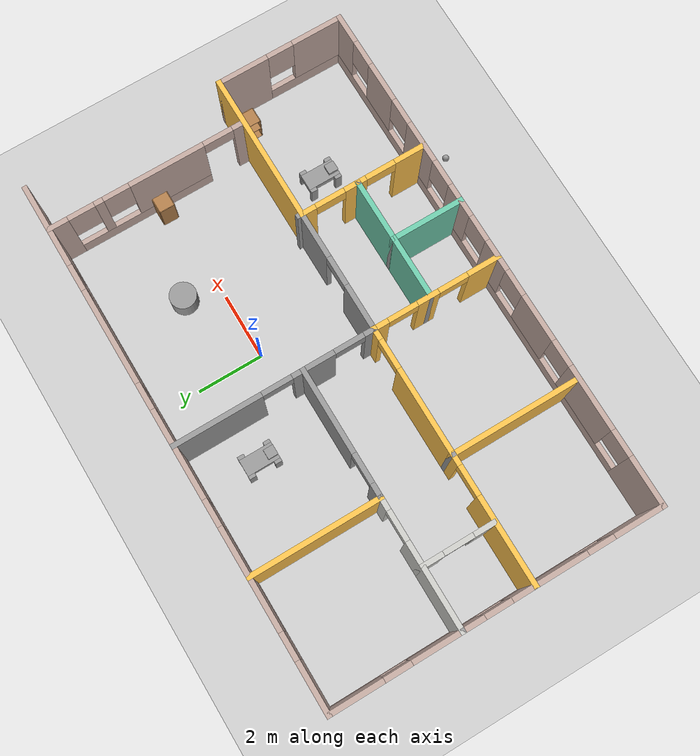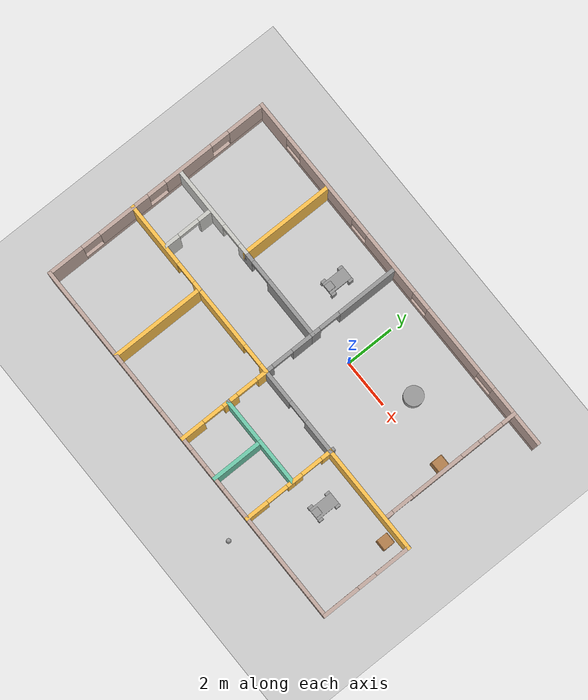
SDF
<sdf version="1.7">
 <world name="default">
  <plugin name="hello" filename="libhello.so"/>
  <light name="sun" type="directional">
   <pose>0 0 10 0 -0 0</pose>
   <diffuse>0.8 0.8 0.8 1</diffuse>
   <specular>0.2 0.2 0.2 1</specular>
   <attenuation>
    <range>1000</range>
    <constant>0.9</constant>
    <linear>0.01</linear>
    <quadratic>0.001</quadratic>
   </attenuation>
   <direction>-0.5 0.1 -0.9</direction>
   <spot><inner_angle>0</inner_angle><outer_angle>0</outer_angle><falloff>0</falloff></spot>
  </light>
  <model name="ground_plane">
   <static>1</static>
   <link name="link">
    <collision name="collision">
     <geometry><plane><normal>0 0 1</normal><size>100 100</size></plane></geometry>
     <surface>
      <contact><collide_bitmask>65535</collide_bitmask></contact>
      <friction><ode><mu>100</mu><mu2>50</mu2></ode></friction>
     </surface>
    </collision>
    <visual name="visual">
     <cast_shadows>0</cast_shadows>
     <geometry><plane><normal>0 0 1</normal><size>100 100</size></plane></geometry>
     <material>
      <script><uri>file://media/materials/scripts/gazebo.material</uri><name>Gazebo/Grey</name></script>
     </material>
    </visual>
   </link>
  </model>
  <gravity>0 0 -9.8</gravity>
  <magnetic_field>6e-06 2.3e-05 -4.2e-05</magnetic_field>
  <atmosphere type="adiabatic"/>
  <physics name="default_physics" default="0" type="ode">
   <max_step_size>0.001</max_step_size>
   <real_time_factor>1</real_time_factor>
   <real_time_update_rate>1000</real_time_update_rate>
  </physics>
  <scene><ambient>0.4 0.4 0.4 1</ambient><background>0.7 0.7 0.7 1</background><shadows>1</shadows></scene>
  <spherical_coordinates>
   <surface_model>EARTH_WGS84</surface_model>
   <latitude_deg>0</latitude_deg>
   <longitude_deg>0</longitude_deg>
   <elevation>0</elevation>
   <heading_deg>0</heading_deg>
  </spherical_coordinates>
  <model name="robothouse">
   <pose>-1.24708 -1.635 0 0 -0 0</pose>
   <link name="Wall_0">
    <pose>0 -4.925 0 0 -0 0</pose>
    <visual name="Wall_0_Visual_0">
     <pose>-7.22766 0 1.25 0 -0 0</pose>
     <geometry><box><size>1.54467 0.15 2.5</size></box></geometry>
     <material>
      <script><uri>file://media/materials/scripts/gazebo.material</uri><name>Gazebo/Grey</name></script>
      <ambient>0.760784 0.662745 0.627451 1</ambient>
     </material>
     <meta><layer>0</layer></meta>
    </visual>
    <collision name="Wall_0_Collision_0">
     <geometry><box><size>1.54467 0.15 2.5</size></box></geometry>
     <pose>-7.22766 0 1.25 0 -0 0</pose>
    </collision>
    <visual name="Wall_0_Visual_1">
     <pose>0.772336 0 0.25 0 -0 0</pose>
     <geometry><box><size>14.4553 0.15 0.5</size></box></geometry>
     <material>
      <script><uri>file://media/materials/scripts/gazebo.material</uri><name>Gazebo/Grey</name></script>
      <ambient>0.760784 0.662745 0.627451 1</ambient>
     </material>
     <meta><layer>0</layer></meta>
    </visual>
    <collision name="Wall_0_Collision_1">
     <geometry><box><size>14.4553 0.15 0.5</size></box></geometry>
     <pose>0.772336 0 0.25 0 -0 0</pose>
    </collision>
    <visual name="Wall_0_Visual_2">
     <pose>-4.67533 0 1.5 0 -0 0</pose>
     <geometry><box><size>1.96 0.15 2</size></box></geometry>
     <material>
      <script><uri>file://media/materials/scripts/gazebo.material</uri><name>Gazebo/Grey</name></script>
      <ambient>0.760784 0.662745 0.627451 1</ambient>
     </material>
     <meta><layer>0</layer></meta>
    </visual>
    <collision name="Wall_0_Collision_2">
     <geometry><box><size>1.96 0.15 2</size></box></geometry>
     <pose>-4.67533 0 1.5 0 -0 0</pose>
    </collision>
    <visual name="Wall_0_Visual_3">
     <pose>-2.18033 0 1.5 0 -0 0</pose>
     <geometry><box><size>1.43 0.15 2</size></box></geometry>
     <material>
      <script><uri>file://media/materials/scripts/gazebo.material</uri><name>Gazebo/Grey</name></script>
      <ambient>0.760784 0.662745 0.627451 1</ambient>
     </material>
     <meta><layer>0</layer></meta>
    </visual>
    <collision name="Wall_0_Collision_3">
     <geometry><box><size>1.43 0.15 2</size></box></geometry>
     <pose>-2.18033 0 1.5 0 -0 0</pose>
    </collision>
    <visual name="Wall_0_Visual_4">
     <pose>-0.180328 0 1.5 0 -0 0</pose>
     <geometry><box><size>0.97 0.15 2</size></box></geometry>
     <material>
      <script><uri>file://media/materials/scripts/gazebo.material</uri><name>Gazebo/Grey</name></script>
      <ambient>0.760784 0.662745 0.627451 1</ambient>
     </material>
     <meta><layer>0</layer></meta>
    </visual>
    <collision name="Wall_0_Collision_4">
     <geometry><box><size>0.97 0.15 2</size></box></geometry>
     <pose>-0.180328 0 1.5 0 -0 0</pose>
    </collision>
    <visual name="Wall_0_Visual_5">
     <pose>1.62467 0 1.5 0 -0 0</pose>
     <geometry><box><size>1.04 0.15 2</size></box></geometry>
     <material>
      <script><uri>file://media/materials/scripts/gazebo.material</uri><name>Gazebo/Grey</name></script>
      <ambient>0.760784 0.662745 0.627451 1</ambient>
     </material>
     <meta><layer>0</layer></meta>
    </visual>
    <collision name="Wall_0_Collision_5">
     <geometry><box><size>1.04 0.15 2</size></box></geometry>
     <pose>1.62467 0 1.5 0 -0 0</pose>
    </collision>
    <visual name="Wall_0_Visual_6">
     <pose>3.58967 0 1.5 0 -0 0</pose>
     <geometry><box><size>1.29 0.15 2</size></box></geometry>
     <material>
      <script><uri>file://media/materials/scripts/gazebo.material</uri><name>Gazebo/Grey</name></script>
      <ambient>0.760784 0.662745 0.627451 1</ambient>
     </material>
     <meta><layer>0</layer></meta>
    </visual>
    <collision name="Wall_0_Collision_6">
     <geometry><box><size>1.29 0.15 2</size></box></geometry>
     <pose>3.58967 0 1.5 0 -0 0</pose>
    </collision>
    <visual name="Wall_0_Visual_7">
     <pose>5.64967 0 1.5 0 -0 0</pose>
     <geometry><box><size>1.23 0.15 2</size></box></geometry>
     <material>
      <script><uri>file://media/materials/scripts/gazebo.material</uri><name>Gazebo/Grey</name></script>
      <ambient>0.760784 0.662745 0.627451 1</ambient>
     </material>
     <meta><layer>0</layer></meta>
    </visual>
    <collision name="Wall_0_Collision_7">
     <geometry><box><size>1.23 0.15 2</size></box></geometry>
     <pose>5.64967 0 1.5 0 -0 0</pose>
    </collision>
    <visual name="Wall_0_Visual_8">
     <pose>7.53234 0 1.5 0 -0 0</pose>
     <geometry><box><size>0.935327 0.15 2</size></box></geometry>
     <material>
      <script><uri>file://media/materials/scripts/gazebo.material</uri><name>Gazebo/Grey</name></script>
      <ambient>0.760784 0.662745 0.627451 1</ambient>
     </material>
     <meta><layer>0</layer></meta>
    </visual>
    <collision name="Wall_0_Collision_8">
     <geometry><box><size>0.935327 0.15 2</size></box></geometry>
     <pose>7.53234 0 1.5 0 -0 0</pose>
    </collision>
    <visual name="Wall_0_Visual_9">
     <pose>-6.05533 0 1.9 0 -0 0</pose>
     <geometry><box><size>0.8 0.15 1.2</size></box></geometry>
     <material>
      <script><uri>file://media/materials/scripts/gazebo.material</uri><name>Gazebo/Grey</name></script>
      <ambient>0.760784 0.662745 0.627451 1</ambient>
     </material>
     <meta><layer>0</layer></meta>
    </visual>
    <collision name="Wall_0_Collision_9">
     <geometry><box><size>0.8 0.15 1.2</size></box></geometry>
     <pose>-6.05533 0 1.9 0 -0 0</pose>
    </collision>
    <visual name="Wall_0_Visual_10">
     <pose>-3.29533 0 1.9 0 -0 0</pose>
     <geometry><box><size>0.8 0.15 1.2</size></box></geometry>
     <material>
      <script><uri>file://media/materials/scripts/gazebo.material</uri><name>Gazebo/Grey</name></script>
      <ambient>0.760784 0.662745 0.627451 1</ambient>
     </material>
     <meta><layer>0</layer></meta>
    </visual>
    <collision name="Wall_0_Collision_10">
     <geometry><box><size>0.8 0.15 1.2</size></box></geometry>
     <pose>-3.29533 0 1.9 0 -0 0</pose>
    </collision>
    <visual name="Wall_0_Visual_11">
     <pose>-1.06533 0 1.9 0 -0 0</pose>
     <geometry><box><size>0.8 0.15 1.2</size></box></geometry>
     <material>
      <script><uri>file://media/materials/scripts/gazebo.material</uri><name>Gazebo/Grey</name></script>
      <ambient>0.760784 0.662745 0.627451 1</ambient>
     </material>
     <meta><layer>0</layer></meta>
    </visual>
    <collision name="Wall_0_Collision_11">
     <geometry><box><size>0.8 0.15 1.2</size></box></geometry>
     <pose>-1.06533 0 1.9 0 -0 0</pose>
    </collision>
    <visual name="Wall_0_Visual_12">
     <pose>0.704672 0 1.9 0 -0 0</pose>
     <geometry><box><size>0.8 0.15 1.2</size></box></geometry>
     <material>
      <script><uri>file://media/materials/scripts/gazebo.material</uri><name>Gazebo/Grey</name></script>
      <ambient>0.760784 0.662745 0.627451 1</ambient>
     </material>
     <meta><layer>0</layer></meta>
    </visual>
    <collision name="Wall_0_Collision_12">
     <geometry><box><size>0.8 0.15 1.2</size></box></geometry>
     <pose>0.704672 0 1.9 0 -0 0</pose>
    </collision>
    <visual name="Wall_0_Visual_13">
     <pose>2.54467 0 1.9 0 -0 0</pose>
     <geometry><box><size>0.8 0.15 1.2</size></box></geometry>
     <material>
      <script><uri>file://media/materials/scripts/gazebo.material</uri><name>Gazebo/Grey</name></script>
      <ambient>0.760784 0.662745 0.627451 1</ambient>
     </material>
     <meta><layer>0</layer></meta>
    </visual>
    <collision name="Wall_0_Collision_13">
     <geometry><box><size>0.8 0.15 1.2</size></box></geometry>
     <pose>2.54467 0 1.9 0 -0 0</pose>
    </collision>
    <visual name="Wall_0_Visual_14">
     <pose>4.63467 0 1.9 0 -0 0</pose>
     <geometry><box><size>0.8 0.15 1.2</size></box></geometry>
     <material>
      <script><uri>file://media/materials/scripts/gazebo.material</uri><name>Gazebo/Grey</name></script>
      <ambient>0.760784 0.662745 0.627451 1</ambient>
     </material>
     <meta><layer>0</layer></meta>
    </visual>
    <collision name="Wall_0_Collision_14">
     <geometry><box><size>0.8 0.15 1.2</size></box></geometry>
     <pose>4.63467 0 1.9 0 -0 0</pose>
    </collision>
    <visual name="Wall_0_Visual_15">
     <pose>6.66467 0 1.9 0 -0 0</pose>
     <geometry><box><size>0.8 0.15 1.2</size></box></geometry>
     <material>
      <script><uri>file://media/materials/scripts/gazebo.material</uri><name>Gazebo/Grey</name></script>
      <ambient>0.760784 0.662745 0.627451 1</ambient>
     </material>
     <meta><layer>0</layer></meta>
    </visual>
    <collision name="Wall_0_Collision_15">
     <geometry><box><size>0.8 0.15 1.2</size></box></geometry>
     <pose>6.66467 0 1.9 0 -0 0</pose>
    </collision>
   </link>
   <link name="Wall_10">
    <collision name="Wall_10_Collision">
     <geometry><box><size>4 0.15 2.5</size></box></geometry>
     <pose>0 0 1.25 0 -0 0</pose>
    </collision>
    <visual name="Wall_10_Visual">
     <pose>0 0 1.25 0 -0 0</pose>
     <geometry><box><size>4 0.15 2.5</size></box></geometry>
     <material>
      <script><uri>file://media/materials/scripts/gazebo.material</uri><name>Gazebo/Grey</name></script>
      <ambient>1 0.764706 0.305882 1</ambient>
     </material>
     <meta><layer>0</layer></meta>
    </visual>
    <pose>-4.075 -3 0 0 -0 -1.5708</pose>
   </link>
   <link name="Wall_13">
    <collision name="Wall_13_Collision">
     <geometry><box><size>0.15 0.15 2.5</size></box></geometry>
     <pose>0 0 1.25 0 -0 0</pose>
    </collision>
    <visual name="Wall_13_Visual">
     <pose>0 0 1.25 0 -0 0</pose>
     <geometry><box><size>0.15 0.15 2.5</size></box></geometry>
     <material>
      <script><uri>file://media/materials/scripts/gazebo.material</uri><name>Gazebo/Grey</name></script>
      <ambient>1 1 1 1</ambient>
     </material>
     <meta><layer>0</layer></meta>
    </visual>
    <pose>-7.925 1.075 0 0 -0 0</pose>
   </link>
   <link name="Wall_14">
    <pose>-6 1.075 0 0 -0 0</pose>
    <visual name="Wall_14_Visual_0">
     <pose>-0.673769 0 1.25 0 -0 0</pose>
     <geometry><box><size>2.65246 0.15 2.5</size></box></geometry>
     <material>
      <script><uri>file://media/materials/scripts/gazebo.material</uri><name>Gazebo/CeilingTiled</name></script>
      <ambient>1 0.764706 0.305882 1</ambient>
     </material>
     <meta><layer>0</layer></meta>
    </visual>
    <collision name="Wall_14_Collision_0">
     <geometry><box><size>2.65246 0.15 2.5</size></box></geometry>
     <pose>-0.673769 0 1.25 0 -0 0</pose>
    </collision>
    <visual name="Wall_14_Visual_1">
     <pose>1.77623 0 1.25 0 -0 0</pose>
     <geometry><box><size>0.447537 0.15 2.5</size></box></geometry>
     <material>
      <script><uri>file://media/materials/scripts/gazebo.material</uri><name>Gazebo/CeilingTiled</name></script>
      <ambient>1 0.764706 0.305882 1</ambient>
     </material>
     <meta><layer>0</layer></meta>
    </visual>
    <collision name="Wall_14_Collision_1">
     <geometry><box><size>0.447537 0.15 2.5</size></box></geometry>
     <pose>1.77623 0 1.25 0 -0 0</pose>
    </collision>
    <visual name="Wall_14_Visual_2">
     <pose>1.10246 0 2.25 0 -0 0</pose>
     <geometry><box><size>0.9 0.15 0.5</size></box></geometry>
     <material>
      <script><uri>file://media/materials/scripts/gazebo.material</uri><name>Gazebo/CeilingTiled</name></script>
      <ambient>1 0.764706 0.305882 1</ambient>
     </material>
     <meta><layer>0</layer></meta>
    </visual>
    <collision name="Wall_14_Collision_2">
     <geometry><box><size>0.9 0.15 0.5</size></box></geometry>
     <pose>1.10246 0 2.25 0 -0 0</pose>
    </collision>
   </link>
   <link name="Wall_15">
    <collision name="Wall_15_Collision">
     <geometry><box><size>0.15 0.15 2.5</size></box></geometry>
     <pose>0 0 1.25 0 -0 0</pose>
    </collision>
    <visual name="Wall_15_Visual">
     <pose>0 0 1.25 0 -0 0</pose>
     <geometry><box><size>0.15 0.15 2.5</size></box></geometry>
     <material>
      <script><uri>file://media/materials/scripts/gazebo.material</uri><name>Gazebo/Grey</name></script>
      <ambient>1 1 1 1</ambient>
     </material>
     <meta><layer>0</layer></meta>
    </visual>
    <pose>-4.075 1.075 0 0 -0 0</pose>
   </link>
   <link name="Wall_16">
    <collision name="Wall_16_Collision">
     <geometry><box><size>4 0.15 2.5</size></box></geometry>
     <pose>0 0 1.25 0 -0 0</pose>
    </collision>
    <visual name="Wall_16_Visual">
     <pose>0 0 1.25 0 -0 0</pose>
     <geometry><box><size>4 0.15 2.5</size></box></geometry>
     <material>
      <script><uri>file://media/materials/scripts/gazebo.material</uri><name>Gazebo/Grey</name></script>
      <ambient>1 0.764706 0.305882 1</ambient>
     </material>
     <meta><layer>0</layer></meta>
    </visual>
    <pose>-4.075 3 0 0 -0 1.5708</pose>
   </link>
   <link name="Wall_2">
    <pose>-7.925 -0 0 0 -0 1.5708</pose>
    <visual name="Wall_2_Visual_0">
     <pose>-4.22011 0 1.25 0 -0 0</pose>
     <geometry><box><size>1.55978 0.15 2.5</size></box></geometry>
     <material>
      <script><uri>file://media/materials/scripts/gazebo.material</uri><name>Gazebo/Grey</name></script>
      <ambient>0.760784 0.662745 0.627451 1</ambient>
     </material>
     <meta><layer>0</layer></meta>
    </visual>
    <collision name="Wall_2_Collision_0">
     <geometry><box><size>1.55978 0.15 2.5</size></box></geometry>
     <pose>-4.22011 0 1.25 0 -0 0</pose>
    </collision>
    <visual name="Wall_2_Visual_1">
     <pose>0.77989 0 0.25 0 -0 0</pose>
     <geometry><box><size>8.44022 0.15 0.5</size></box></geometry>
     <material>
      <script><uri>file://media/materials/scripts/gazebo.material</uri><name>Gazebo/Grey</name></script>
      <ambient>0.760784 0.662745 0.627451 1</ambient>
     </material>
     <meta><layer>0</layer></meta>
    </visual>
    <collision name="Wall_2_Collision_1">
     <geometry><box><size>8.44022 0.15 0.5</size></box></geometry>
     <pose>0.77989 0 0.25 0 -0 0</pose>
    </collision>
    <visual name="Wall_2_Visual_2">
     <pose>-1.51522 0 1.5 0 -0 0</pose>
     <geometry><box><size>2.25 0.15 2</size></box></geometry>
     <material>
      <script><uri>file://media/materials/scripts/gazebo.material</uri><name>Gazebo/Grey</name></script>
      <ambient>0.760784 0.662745 0.627451 1</ambient>
     </material>
     <meta><layer>0</layer></meta>
    </visual>
    <collision name="Wall_2_Collision_2">
     <geometry><box><size>2.25 0.15 2</size></box></geometry>
     <pose>-1.51522 0 1.5 0 -0 0</pose>
    </collision>
    <visual name="Wall_2_Visual_3">
     <pose>1.47335 0 1.5 0 -0 0</pose>
     <geometry><box><size>2.12714 0.15 2</size></box></geometry>
     <material>
      <script><uri>file://media/materials/scripts/gazebo.material</uri><name>Gazebo/Grey</name></script>
      <ambient>0.760784 0.662745 0.627451 1</ambient>
     </material>
     <meta><layer>0</layer></meta>
    </visual>
    <collision name="Wall_2_Collision_3">
     <geometry><box><size>2.12714 0.15 2</size></box></geometry>
     <pose>1.47335 0 1.5 0 -0 0</pose>
    </collision>
    <visual name="Wall_2_Visual_4">
     <pose>4.16846 0 1.5 0 -0 0</pose>
     <geometry><box><size>1.66308 0.15 2</size></box></geometry>
     <material>
      <script><uri>file://media/materials/scripts/gazebo.material</uri><name>Gazebo/Grey</name></script>
      <ambient>0.760784 0.662745 0.627451 1</ambient>
     </material>
     <meta><layer>0</layer></meta>
    </visual>
    <collision name="Wall_2_Collision_4">
     <geometry><box><size>1.66308 0.15 2</size></box></geometry>
     <pose>4.16846 0 1.5 0 -0 0</pose>
    </collision>
    <visual name="Wall_2_Visual_5">
     <pose>-3.04022 0 1.9 0 -0 0</pose>
     <geometry><box><size>0.8 0.15 1.2</size></box></geometry>
     <material>
      <script><uri>file://media/materials/scripts/gazebo.material</uri><name>Gazebo/Grey</name></script>
      <ambient>0.760784 0.662745 0.627451 1</ambient>
     </material>
     <meta><layer>0</layer></meta>
    </visual>
    <collision name="Wall_2_Collision_5">
     <geometry><box><size>0.8 0.15 1.2</size></box></geometry>
     <pose>-3.04022 0 1.9 0 -0 0</pose>
    </collision>
    <visual name="Wall_2_Visual_6">
     <pose>0.00978 0 1.9 0 -0 0</pose>
     <geometry><box><size>0.8 0.15 1.2</size></box></geometry>
     <material>
      <script><uri>file://media/materials/scripts/gazebo.material</uri><name>Gazebo/Grey</name></script>
      <ambient>0.760784 0.662745 0.627451 1</ambient>
     </material>
     <meta><layer>0</layer></meta>
    </visual>
    <collision name="Wall_2_Collision_6">
     <geometry><box><size>0.8 0.15 1.2</size></box></geometry>
     <pose>0.00978 0 1.9 0 -0 0</pose>
    </collision>
    <visual name="Wall_2_Visual_7">
     <pose>2.93692 0 1.9 0 -0 0</pose>
     <geometry><box><size>0.8 0.15 1.2</size></box></geometry>
     <material>
      <script><uri>file://media/materials/scripts/gazebo.material</uri><name>Gazebo/Grey</name></script>
      <ambient>0.760784 0.662745 0.627451 1</ambient>
     </material>
     <meta><layer>0</layer></meta>
    </visual>
    <collision name="Wall_2_Collision_7">
     <geometry><box><size>0.8 0.15 1.2</size></box></geometry>
     <pose>2.93692 0 1.9 0 -0 0</pose>
    </collision>
   </link>
   <link name="Wall_21">
    <pose>-2.15 -1.075 0 0 -0 0</pose>
    <visual name="Wall_21_Visual_0">
     <pose>-0.654694 0 1.25 0 -0 0</pose>
     <geometry><box><size>2.69061 0.15 2.5</size></box></geometry>
     <material>
      <script><uri>file://media/materials/scripts/gazebo.material</uri><name>Gazebo/Grey</name></script>
      <ambient>1 0.764706 0.305882 1</ambient>
     </material>
     <meta><layer>0</layer></meta>
    </visual>
    <collision name="Wall_21_Collision_0">
     <geometry><box><size>2.69061 0.15 2.5</size></box></geometry>
     <pose>-0.654694 0 1.25 0 -0 0</pose>
    </collision>
    <visual name="Wall_21_Visual_1">
     <pose>1.79531 0 1.25 0 -0 0</pose>
     <geometry><box><size>0.409387 0.15 2.5</size></box></geometry>
     <material>
      <script><uri>file://media/materials/scripts/gazebo.material</uri><name>Gazebo/Grey</name></script>
      <ambient>1 0.764706 0.305882 1</ambient>
     </material>
     <meta><layer>0</layer></meta>
    </visual>
    <collision name="Wall_21_Collision_1">
     <geometry><box><size>0.409387 0.15 2.5</size></box></geometry>
     <pose>1.79531 0 1.25 0 -0 0</pose>
    </collision>
    <visual name="Wall_21_Visual_2">
     <pose>1.14061 0 2.25 0 -0 0</pose>
     <geometry><box><size>0.9 0.15 0.5</size></box></geometry>
     <material>
      <script><uri>file://media/materials/scripts/gazebo.material</uri><name>Gazebo/Grey</name></script>
      <ambient>1 0.764706 0.305882 1</ambient>
     </material>
     <meta><layer>0</layer></meta>
    </visual>
    <collision name="Wall_21_Collision_2">
     <geometry><box><size>0.9 0.15 0.5</size></box></geometry>
     <pose>1.14061 0 2.25 0 -0 0</pose>
    </collision>
   </link>
   <link name="Wall_22">
    <collision name="Wall_22_Collision">
     <geometry><box><size>0.15 0.15 2.5</size></box></geometry>
     <pose>0 0 1.25 0 -0 0</pose>
    </collision>
    <visual name="Wall_22_Visual">
     <pose>0 0 1.25 0 -0 0</pose>
     <geometry><box><size>0.15 0.15 2.5</size></box></geometry>
     <material>
      <script><uri>file://media/materials/scripts/gazebo.material</uri><name>Gazebo/Grey</name></script>
      <ambient>1 1 1 1</ambient>
     </material>
     <meta><layer>0</layer></meta>
    </visual>
    <pose>-0.225 -1.075 0 0 -0 0</pose>
   </link>
   <link name="Wall_26">
    <pose>-0.225 -3 0 0 -0 -1.5708</pose>
    <visual name="Wall_26_Visual_0">
     <pose>-1.74489 0 1.25 0 -0 0</pose>
     <geometry><box><size>0.51022 0.15 2.5</size></box></geometry>
     <material>
      <script><uri>file://media/materials/scripts/gazebo.material</uri><name>Gazebo/Grey</name></script>
      <ambient>1 0.764706 0.305882 1</ambient>
     </material>
     <meta><layer>0</layer></meta>
    </visual>
    <collision name="Wall_26_Collision_0">
     <geometry><box><size>0.51022 0.15 2.5</size></box></geometry>
     <pose>-1.74489 0 1.25 0 -0 0</pose>
    </collision>
    <visual name="Wall_26_Visual_1">
     <pose>-0.25978 0 1.25 0 -0 0</pose>
     <geometry><box><size>0.66 0.15 2.5</size></box></geometry>
     <material>
      <script><uri>file://media/materials/scripts/gazebo.material</uri><name>Gazebo/Grey</name></script>
      <ambient>1 0.764706 0.305882 1</ambient>
     </material>
     <meta><layer>0</layer></meta>
    </visual>
    <collision name="Wall_26_Collision_1">
     <geometry><box><size>0.66 0.15 2.5</size></box></geometry>
     <pose>-0.25978 0 1.25 0 -0 0</pose>
    </collision>
    <visual name="Wall_26_Visual_2">
     <pose>1.48511 0 1.25 0 -0 0</pose>
     <geometry><box><size>1.02978 0.15 2.5</size></box></geometry>
     <material>
      <script><uri>file://media/materials/scripts/gazebo.material</uri><name>Gazebo/Grey</name></script>
      <ambient>1 0.764706 0.305882 1</ambient>
     </material>
     <meta><layer>0</layer></meta>
    </visual>
    <collision name="Wall_26_Collision_2">
     <geometry><box><size>1.02978 0.15 2.5</size></box></geometry>
     <pose>1.48511 0 1.25 0 -0 0</pose>
    </collision>
    <visual name="Wall_26_Visual_3">
     <pose>-1.03978 0 2.25 0 -0 0</pose>
     <geometry><box><size>0.9 0.15 0.5</size></box></geometry>
     <material>
      <script><uri>file://media/materials/scripts/gazebo.material</uri><name>Gazebo/Grey</name></script>
      <ambient>1 0.764706 0.305882 1</ambient>
     </material>
     <meta><layer>0</layer></meta>
    </visual>
    <collision name="Wall_26_Collision_3">
     <geometry><box><size>0.9 0.15 0.5</size></box></geometry>
     <pose>-1.03978 0 2.25 0 -0 0</pose>
    </collision>
    <visual name="Wall_26_Visual_4">
     <pose>0.52022 0 2.25 0 -0 0</pose>
     <geometry><box><size>0.9 0.15 0.5</size></box></geometry>
     <material>
      <script><uri>file://media/materials/scripts/gazebo.material</uri><name>Gazebo/Grey</name></script>
      <ambient>1 0.764706 0.305882 1</ambient>
     </material>
     <meta><layer>0</layer></meta>
    </visual>
    <collision name="Wall_26_Collision_4">
     <geometry><box><size>0.9 0.15 0.5</size></box></geometry>
     <pose>0.52022 0 2.25 0 -0 0</pose>
    </collision>
   </link>
   <link name="Wall_28">
    <collision name="Wall_28_Collision">
     <geometry><box><size>0.15 0.15 2.5</size></box></geometry>
     <pose>0 0 1.25 0 -0 0</pose>
    </collision>
    <visual name="Wall_28_Visual">
     <pose>0 0 1.25 0 -0 0</pose>
     <geometry><box><size>0.15 0.15 2.5</size></box></geometry>
     <material>
      <script><uri>file://media/materials/scripts/gazebo.material</uri><name>Gazebo/Grey</name></script>
      <ambient>1 1 1 1</ambient>
     </material>
     <meta><layer>0</layer></meta>
    </visual>
    <pose>-0.225 -2.825 0 0 -0 0</pose>
   </link>
   <link name="Wall_29">
    <collision name="Wall_29_Collision">
     <geometry><box><size>2 0.15 2.5</size></box></geometry>
     <pose>0 0 1.25 0 -0 0</pose>
    </collision>
    <visual name="Wall_29_Visual">
     <pose>0 0 1.25 0 -0 0</pose>
     <geometry><box><size>2 0.15 2.5</size></box></geometry>
     <material>
      <script><uri>file://media/materials/scripts/gazebo.material</uri><name>Gazebo/Grey</name></script>
      <ambient>0.435294 0.796078 0.67451 1</ambient>
     </material>
     <meta><layer>0</layer></meta>
    </visual>
    <pose>0.700001 -2.825 0 0 -0 0</pose>
   </link>
   <link name="Wall_30">
    <collision name="Wall_30_Collision">
     <geometry><box><size>0.15 0.15 2.5</size></box></geometry>
     <pose>0 0 1.25 0 -0 0</pose>
    </collision>
    <visual name="Wall_30_Visual">
     <pose>0 0 1.25 0 -0 0</pose>
     <geometry><box><size>0.15 0.15 2.5</size></box></geometry>
     <material>
      <script><uri>file://media/materials/scripts/gazebo.material</uri><name>Gazebo/Grey</name></script>
      <ambient>1 1 1 1</ambient>
     </material>
     <meta><layer>0</layer></meta>
    </visual>
    <pose>1.625 -2.825 0 0 -0 0</pose>
   </link>
   <link name="Wall_31">
    <collision name="Wall_31_Collision">
     <geometry><box><size>2.25 0.15 2.5</size></box></geometry>
     <pose>0 0 1.25 0 -0 0</pose>
    </collision>
    <visual name="Wall_31_Visual">
     <pose>0 0 1.25 0 -0 0</pose>
     <geometry><box><size>2.25 0.15 2.5</size></box></geometry>
     <material>
      <script><uri>file://media/materials/scripts/gazebo.material</uri><name>Gazebo/Grey</name></script>
      <ambient>0.435294 0.796078 0.67451 1</ambient>
     </material>
     <meta><layer>0</layer></meta>
    </visual>
    <pose>1.625 -3.875 0 0 -0 -1.5708</pose>
   </link>
   <link name="Wall_33">
    <collision name="Wall_33_Collision">
     <geometry><box><size>2 0.15 2.5</size></box></geometry>
     <pose>0 0 1.25 0 -0 0</pose>
    </collision>
    <visual name="Wall_33_Visual">
     <pose>0 0 1.25 0 -0 0</pose>
     <geometry><box><size>2 0.15 2.5</size></box></geometry>
     <material>
      <script><uri>file://media/materials/scripts/gazebo.material</uri><name>Gazebo/Grey</name></script>
      <ambient>0.435294 0.796078 0.67451 1</ambient>
     </material>
     <meta><layer>0</layer></meta>
    </visual>
    <pose>2.55 -2.825 0 0 -0 0</pose>
   </link>
   <link name="Wall_34">
    <collision name="Wall_34_Collision">
     <geometry><box><size>0.15 0.15 2.5</size></box></geometry>
     <pose>0 0 1.25 0 -0 0</pose>
    </collision>
    <visual name="Wall_34_Visual">
     <pose>0 0 1.25 0 -0 0</pose>
     <geometry><box><size>0.15 0.15 2.5</size></box></geometry>
     <material>
      <script><uri>file://media/materials/scripts/gazebo.material</uri><name>Gazebo/Grey</name></script>
      <ambient>1 1 1 1</ambient>
     </material>
     <meta><layer>0</layer></meta>
    </visual>
    <pose>3.475 -2.825 0 0 -0 0</pose>
   </link>
   <link name="Wall_35">
    <pose>3.475 -3.875 0 0 -0 -1.5708</pose>
    <visual name="Wall_35_Visual_0">
     <pose>-0.95989 0 1.25 0 -0 0</pose>
     <geometry><box><size>0.33022 0.15 2.5</size></box></geometry>
     <material>
      <script><uri>file://media/materials/scripts/gazebo.material</uri><name>Gazebo/Grey</name></script>
      <ambient>1 0.764706 0.305882 1</ambient>
     </material>
     <meta><layer>0</layer></meta>
    </visual>
    <collision name="Wall_35_Collision_0">
     <geometry><box><size>0.33022 0.15 2.5</size></box></geometry>
     <pose>-0.95989 0 1.25 0 -0 0</pose>
    </collision>
    <visual name="Wall_35_Visual_1">
     <pose>0.61511 0 1.25 0 -0 0</pose>
     <geometry><box><size>1.01978 0.15 2.5</size></box></geometry>
     <material>
      <script><uri>file://media/materials/scripts/gazebo.material</uri><name>Gazebo/Grey</name></script>
      <ambient>1 0.764706 0.305882 1</ambient>
     </material>
     <meta><layer>0</layer></meta>
    </visual>
    <collision name="Wall_35_Collision_1">
     <geometry><box><size>1.01978 0.15 2.5</size></box></geometry>
     <pose>0.61511 0 1.25 0 -0 0</pose>
    </collision>
    <visual name="Wall_35_Visual_2">
     <pose>-0.34478 0 2.25 0 -0 0</pose>
     <geometry><box><size>0.9 0.15 0.5</size></box></geometry>
     <material>
      <script><uri>file://media/materials/scripts/gazebo.material</uri><name>Gazebo/Grey</name></script>
      <ambient>1 0.764706 0.305882 1</ambient>
     </material>
     <meta><layer>0</layer></meta>
    </visual>
    <collision name="Wall_35_Collision_2">
     <geometry><box><size>0.9 0.15 0.5</size></box></geometry>
     <pose>-0.34478 0 2.25 0 -0 0</pose>
    </collision>
   </link>
   <link name="Wall_38">
    <collision name="Wall_38_Collision">
     <geometry><box><size>0.15 0.15 2.5</size></box></geometry>
     <pose>0 0 1.25 0 -0 0</pose>
    </collision>
    <visual name="Wall_38_Visual">
     <pose>0 0 1.25 0 -0 0</pose>
     <geometry><box><size>0.15 0.15 2.5</size></box></geometry>
     <material>
      <script><uri>file://media/materials/scripts/gazebo.material</uri><name>Gazebo/Grey</name></script>
      <ambient>1 1 1 1</ambient>
     </material>
     <meta><layer>0</layer></meta>
    </visual>
    <pose>7.925 -1.075 0 0 -0 0</pose>
   </link>
   <link name="Wall_4">
    <pose>0 4.925 0 0 -0 0</pose>
    <visual name="Wall_4_Visual_0">
     <pose>-7.21623 0 1.25 0 -0 0</pose>
     <geometry><box><size>1.56754 0.15 2.5</size></box></geometry>
     <material>
      <script><uri>file://media/materials/scripts/gazebo.material</uri><name>Gazebo/Grey</name></script>
      <ambient>0.760784 0.662745 0.627451 1</ambient>
     </material>
     <meta><layer>0</layer></meta>
    </visual>
    <collision name="Wall_4_Collision_0">
     <geometry><box><size>1.56754 0.15 2.5</size></box></geometry>
     <pose>-7.21623 0 1.25 0 -0 0</pose>
    </collision>
    <visual name="Wall_4_Visual_1">
     <pose>0.783771 0 0.25 0 -0 0</pose>
     <geometry><box><size>14.4325 0.15 0.5</size></box></geometry>
     <material>
      <script><uri>file://media/materials/scripts/gazebo.material</uri><name>Gazebo/Grey</name></script>
      <ambient>0.760784 0.662745 0.627451 1</ambient>
     </material>
     <meta><layer>0</layer></meta>
    </visual>
    <collision name="Wall_4_Collision_1">
     <geometry><box><size>14.4325 0.15 0.5</size></box></geometry>
     <pose>0.783771 0 0.25 0 -0 0</pose>
    </collision>
    <visual name="Wall_4_Visual_2">
     <pose>-4.12376 0 1.5 0 -0 0</pose>
     <geometry><box><size>3.0174 0.15 2</size></box></geometry>
     <material>
      <script><uri>file://media/materials/scripts/gazebo.material</uri><name>Gazebo/Grey</name></script>
      <ambient>0.760784 0.662745 0.627451 1</ambient>
     </material>
     <meta><layer>0</layer></meta>
    </visual>
    <collision name="Wall_4_Collision_2">
     <geometry><box><size>3.0174 0.15 2</size></box></geometry>
     <pose>-4.12376 0 1.5 0 -0 0</pose>
    </collision>
    <visual name="Wall_4_Visual_3">
     <pose>-0.466056 0 1.5 0 -0 0</pose>
     <geometry><box><size>2.69801 0.15 2</size></box></geometry>
     <material>
      <script><uri>file://media/materials/scripts/gazebo.material</uri><name>Gazebo/Grey</name></script>
      <ambient>0.760784 0.662745 0.627451 1</ambient>
     </material>
     <meta><layer>0</layer></meta>
    </visual>
    <collision name="Wall_4_Collision_3">
     <geometry><box><size>2.69801 0.15 2</size></box></geometry>
     <pose>-0.466056 0 1.5 0 -0 0</pose>
    </collision>
    <visual name="Wall_4_Visual_4">
     <pose>3.14602 0 1.5 0 -0 0</pose>
     <geometry><box><size>2.92614 0.15 2</size></box></geometry>
     <material>
      <script><uri>file://media/materials/scripts/gazebo.material</uri><name>Gazebo/Grey</name></script>
      <ambient>0.760784 0.662745 0.627451 1</ambient>
     </material>
     <meta><layer>0</layer></meta>
    </visual>
    <collision name="Wall_4_Collision_4">
     <geometry><box><size>2.92614 0.15 2</size></box></geometry>
     <pose>3.14602 0 1.5 0 -0 0</pose>
    </collision>
    <visual name="Wall_4_Visual_5">
     <pose>6.70455 0 1.5 0 -0 0</pose>
     <geometry><box><size>2.59091 0.15 2</size></box></geometry>
     <material>
      <script><uri>file://media/materials/scripts/gazebo.material</uri><name>Gazebo/Grey</name></script>
      <ambient>0.760784 0.662745 0.627451 1</ambient>
     </material>
     <meta><layer>0</layer></meta>
    </visual>
    <collision name="Wall_4_Collision_5">
     <geometry><box><size>2.59091 0.15 2</size></box></geometry>
     <pose>6.70455 0 1.5 0 -0 0</pose>
    </collision>
    <visual name="Wall_4_Visual_6">
     <pose>-6.03246 0 1.9 0 -0 0</pose>
     <geometry><box><size>0.8 0.15 1.2</size></box></geometry>
     <material>
      <script><uri>file://media/materials/scripts/gazebo.material</uri><name>Gazebo/Grey</name></script>
      <ambient>0.760784 0.662745 0.627451 1</ambient>
     </material>
     <meta><layer>0</layer></meta>
    </visual>
    <collision name="Wall_4_Collision_6">
     <geometry><box><size>0.8 0.15 1.2</size></box></geometry>
     <pose>-6.03246 0 1.9 0 -0 0</pose>
    </collision>
    <visual name="Wall_4_Visual_7">
     <pose>-2.21506 0 1.9 0 -0 0</pose>
     <geometry><box><size>0.8 0.15 1.2</size></box></geometry>
     <material>
      <script><uri>file://media/materials/scripts/gazebo.material</uri><name>Gazebo/Grey</name></script>
      <ambient>0.760784 0.662745 0.627451 1</ambient>
     </material>
     <meta><layer>0</layer></meta>
    </visual>
    <collision name="Wall_4_Collision_7">
     <geometry><box><size>0.8 0.15 1.2</size></box></geometry>
     <pose>-2.21506 0 1.9 0 -0 0</pose>
    </collision>
    <visual name="Wall_4_Visual_8">
     <pose>1.28295 0 1.9 0 -0 0</pose>
     <geometry><box><size>0.8 0.15 1.2</size></box></geometry>
     <material>
      <script><uri>file://media/materials/scripts/gazebo.material</uri><name>Gazebo/Grey</name></script>
      <ambient>0.760784 0.662745 0.627451 1</ambient>
     </material>
     <meta><layer>0</layer></meta>
    </visual>
    <collision name="Wall_4_Collision_8">
     <geometry><box><size>0.8 0.15 1.2</size></box></geometry>
     <pose>1.28295 0 1.9 0 -0 0</pose>
    </collision>
    <visual name="Wall_4_Visual_9">
     <pose>5.00909 0 1.9 0 -0 0</pose>
     <geometry><box><size>0.8 0.15 1.2</size></box></geometry>
     <material>
      <script><uri>file://media/materials/scripts/gazebo.material</uri><name>Gazebo/Grey</name></script>
      <ambient>0.760784 0.662745 0.627451 1</ambient>
     </material>
     <meta><layer>0</layer></meta>
    </visual>
    <collision name="Wall_4_Collision_9">
     <geometry><box><size>0.8 0.15 1.2</size></box></geometry>
     <pose>5.00909 0 1.9 0 -0 0</pose>
    </collision>
   </link>
   <link name="Wall_43">
    <collision name="Wall_43_Collision">
     <geometry><box><size>0.15 0.15 2.5</size></box></geometry>
     <pose>0 0 1.25 0 -0 0</pose>
    </collision>
    <visual name="Wall_43_Visual">
     <pose>0 0 1.25 0 -0 0</pose>
     <geometry><box><size>0.15 0.15 2.5</size></box></geometry>
     <material>
      <script><uri>file://media/materials/scripts/gazebo.material</uri><name>Gazebo/Grey</name></script>
      <ambient>1 1 1 1</ambient>
     </material>
     <meta><layer>0</layer></meta>
    </visual>
    <pose>3.475 -2.825 0 0 -0 0</pose>
   </link>
   <link name="Wall_45">
    <collision name="Wall_45_Collision">
     <geometry><box><size>0.15 0.15 2.5</size></box></geometry>
     <pose>0 0 1.25 0 -0 0</pose>
    </collision>
    <visual name="Wall_45_Visual">
     <pose>0 0 1.25 0 -0 0</pose>
     <geometry><box><size>0.15 0.15 2.5</size></box></geometry>
     <material>
      <script><uri>file://media/materials/scripts/gazebo.material</uri><name>Gazebo/Grey</name></script>
      <ambient>1 1 1 1</ambient>
     </material>
     <meta><layer>0</layer></meta>
    </visual>
    <pose>3.475 -0.975 0 0 -0 0</pose>
   </link>
   <link name="Wall_50">
    <collision name="Wall_50_Collision">
     <geometry><box><size>4.6 0.15 2.5</size></box></geometry>
     <pose>0 0 1.25 0 -0 0</pose>
    </collision>
    <visual name="Wall_50_Visual">
     <pose>0 0 1.25 0 -0 0</pose>
     <geometry><box><size>4.6 0.15 2.5</size></box></geometry>
     <material>
      <script><uri>file://media/materials/scripts/gazebo.material</uri><name>Gazebo/Grey</name></script>
      <ambient>1 0.764706 0.305882 1</ambient>
     </material>
     <meta><layer>0</layer></meta>
    </visual>
    <pose>5.7 -1.075 0 0 -0 0</pose>
   </link>
   <link name="Wall_51">
    <pose>7.925 -3 0 0 -0 -1.5708</pose>
    <visual name="Wall_51_Visual_0">
     <pose>-1.20489 0 1.25 0 -0 0</pose>
     <geometry><box><size>1.59022 0.15 2.5</size></box></geometry>
     <material>
      <script><uri>file://media/materials/scripts/gazebo.material</uri><name>Gazebo/Grey</name></script>
      <ambient>0.760784 0.662745 0.627451 1</ambient>
     </material>
     <meta><layer>0</layer></meta>
    </visual>
    <collision name="Wall_51_Collision_0">
     <geometry><box><size>1.59022 0.15 2.5</size></box></geometry>
     <pose>-1.20489 0 1.25 0 -0 0</pose>
    </collision>
    <visual name="Wall_51_Visual_1">
     <pose>0.79511 0 0.25 0 -0 0</pose>
     <geometry><box><size>2.40978 0.15 0.5</size></box></geometry>
     <material>
      <script><uri>file://media/materials/scripts/gazebo.material</uri><name>Gazebo/Grey</name></script>
      <ambient>0.760784 0.662745 0.627451 1</ambient>
     </material>
     <meta><layer>0</layer></meta>
    </visual>
    <collision name="Wall_51_Collision_1">
     <geometry><box><size>2.40978 0.15 0.5</size></box></geometry>
     <pose>0.79511 0 0.25 0 -0 0</pose>
    </collision>
    <visual name="Wall_51_Visual_2">
     <pose>1.19511 0 1.5 0 -0 0</pose>
     <geometry><box><size>1.60978 0.15 2</size></box></geometry>
     <material>
      <script><uri>file://media/materials/scripts/gazebo.material</uri><name>Gazebo/Grey</name></script>
      <ambient>0.760784 0.662745 0.627451 1</ambient>
     </material>
     <meta><layer>0</layer></meta>
    </visual>
    <collision name="Wall_51_Collision_2">
     <geometry><box><size>1.60978 0.15 2</size></box></geometry>
     <pose>1.19511 0 1.5 0 -0 0</pose>
    </collision>
    <visual name="Wall_51_Visual_3">
     <pose>-0.00978 0 1.9 0 -0 0</pose>
     <geometry><box><size>0.8 0.15 1.2</size></box></geometry>
     <material>
      <script><uri>file://media/materials/scripts/gazebo.material</uri><name>Gazebo/Grey</name></script>
      <ambient>0.760784 0.662745 0.627451 1</ambient>
     </material>
     <meta><layer>0</layer></meta>
    </visual>
    <collision name="Wall_51_Collision_3">
     <geometry><box><size>0.8 0.15 1.2</size></box></geometry>
     <pose>-0.00978 0 1.9 0 -0 0</pose>
    </collision>
   </link>
   <link name="Wall_53">
    <pose>3.475 -1.95 0 0 -0 -1.5708</pose>
    <visual name="Wall_53_Visual_0">
     <pose>-0.69989 0 1.25 0 -0 0</pose>
     <geometry><box><size>0.50022 0.15 2.5</size></box></geometry>
     <material>
      <script><uri>file://media/materials/scripts/gazebo.material</uri><name>Gazebo/Grey</name></script>
      <ambient>1 0.764706 0.305882 1</ambient>
     </material>
     <meta><layer>0</layer></meta>
    </visual>
    <collision name="Wall_53_Collision_0">
     <geometry><box><size>0.50022 0.15 2.5</size></box></geometry>
     <pose>-0.69989 0 1.25 0 -0 0</pose>
    </collision>
    <visual name="Wall_53_Visual_1">
     <pose>0.70011 0 1.25 0 -0 0</pose>
     <geometry><box><size>0.49978 0.15 2.5</size></box></geometry>
     <material>
      <script><uri>file://media/materials/scripts/gazebo.material</uri><name>Gazebo/Grey</name></script>
      <ambient>1 0.764706 0.305882 1</ambient>
     </material>
     <meta><layer>0</layer></meta>
    </visual>
    <collision name="Wall_53_Collision_1">
     <geometry><box><size>0.49978 0.15 2.5</size></box></geometry>
     <pose>0.70011 0 1.25 0 -0 0</pose>
    </collision>
    <visual name="Wall_53_Visual_2">
     <pose>0.00022 0 2.25 0 -0 0</pose>
     <geometry><box><size>0.9 0.15 0.5</size></box></geometry>
     <material>
      <script><uri>file://media/materials/scripts/gazebo.material</uri><name>Gazebo/Grey</name></script>
      <ambient>1 0.764706 0.305882 1</ambient>
     </material>
     <meta><layer>0</layer></meta>
    </visual>
    <collision name="Wall_53_Collision_2">
     <geometry><box><size>0.9 0.15 0.5</size></box></geometry>
     <pose>0.00022 0 2.25 0 -0 0</pose>
    </collision>
   </link>
   <link name="Wall_58">
    <pose>-2.15 1.075 0 0 -0 0</pose>
    <visual name="Wall_58_Visual_0">
     <pose>-1.75237 0 1.25 0 -0 0</pose>
     <geometry><box><size>0.495263 0.15 2.5</size></box></geometry>
     <material>
      <script><uri>file://media/materials/scripts/gazebo.material</uri><name>Gazebo/Grey</name></script>
      <ambient>1 1 1 1</ambient>
     </material>
     <meta><layer>0</layer></meta>
    </visual>
    <collision name="Wall_58_Collision_0">
     <geometry><box><size>0.495263 0.15 2.5</size></box></geometry>
     <pose>-1.75237 0 1.25 0 -0 0</pose>
    </collision>
    <visual name="Wall_58_Visual_1">
     <pose>0.697631 0 1.25 0 -0 0</pose>
     <geometry><box><size>2.60474 0.15 2.5</size></box></geometry>
     <material>
      <script><uri>file://media/materials/scripts/gazebo.material</uri><name>Gazebo/Grey</name></script>
      <ambient>1 1 1 1</ambient>
     </material>
     <meta><layer>0</layer></meta>
    </visual>
    <collision name="Wall_58_Collision_1">
     <geometry><box><size>2.60474 0.15 2.5</size></box></geometry>
     <pose>0.697631 0 1.25 0 -0 0</pose>
    </collision>
    <visual name="Wall_58_Visual_2">
     <pose>-1.05474 0 2.25 0 -0 0</pose>
     <geometry><box><size>0.9 0.15 0.5</size></box></geometry>
     <material>
      <script><uri>file://media/materials/scripts/gazebo.material</uri><name>Gazebo/Grey</name></script>
      <ambient>1 1 1 1</ambient>
     </material>
     <meta><layer>0</layer></meta>
    </visual>
    <collision name="Wall_58_Collision_2">
     <geometry><box><size>0.9 0.15 0.5</size></box></geometry>
     <pose>-1.05474 0 2.25 0 -0 0</pose>
    </collision>
   </link>
   <link name="Wall_61">
    <pose>-0.225 3 0 0 -0 1.5708</pose>
    <visual name="Wall_61_Visual_0">
     <pose>-1.79201 0 1.25 0 -0 0</pose>
     <geometry><box><size>0.415971 0.15 2.5</size></box></geometry>
     <material>
      <script><uri>file://media/materials/scripts/gazebo.material</uri><name>Gazebo/Grey</name></script>
      <ambient>1 1 1 1</ambient>
     </material>
     <meta><layer>0</layer></meta>
    </visual>
    <collision name="Wall_61_Collision_0">
     <geometry><box><size>0.415971 0.15 2.5</size></box></geometry>
     <pose>-1.79201 0 1.25 0 -0 0</pose>
    </collision>
    <visual name="Wall_61_Visual_1">
     <pose>0.657985 0 1.25 0 -0 0</pose>
     <geometry><box><size>2.68403 0.15 2.5</size></box></geometry>
     <material>
      <script><uri>file://media/materials/scripts/gazebo.material</uri><name>Gazebo/Grey</name></script>
      <ambient>1 1 1 1</ambient>
     </material>
     <meta><layer>0</layer></meta>
    </visual>
    <collision name="Wall_61_Collision_1">
     <geometry><box><size>2.68403 0.15 2.5</size></box></geometry>
     <pose>0.657985 0 1.25 0 -0 0</pose>
    </collision>
    <visual name="Wall_61_Visual_2">
     <pose>-1.13403 0 2.25 0 -0 0</pose>
     <geometry><box><size>0.9 0.15 0.5</size></box></geometry>
     <material>
      <script><uri>file://media/materials/scripts/gazebo.material</uri><name>Gazebo/Grey</name></script>
      <ambient>1 1 1 1</ambient>
     </material>
     <meta><layer>0</layer></meta>
    </visual>
    <collision name="Wall_61_Collision_2">
     <geometry><box><size>0.9 0.15 0.5</size></box></geometry>
     <pose>-1.13403 0 2.25 0 -0 0</pose>
    </collision>
   </link>
   <link name="Wall_68">
    <pose>6.575 2 0 0 -0 -1.5708</pose>
    <visual name="Wall_68_Visual_0">
     <pose>-2.67795 0 1.25 0 -0 0</pose>
     <geometry><box><size>0.644092 0.15 2.5</size></box></geometry>
     <material>
      <script><uri>file://media/materials/scripts/gazebo.material</uri><name>Gazebo/Grey</name></script>
      <ambient>0.760784 0.662745 0.627451 1</ambient>
     </material>
     <meta><layer>0</layer></meta>
    </visual>
    <collision name="Wall_68_Collision_0">
     <geometry><box><size>0.644092 0.15 2.5</size></box></geometry>
     <pose>-2.67795 0 1.25 0 -0 0</pose>
    </collision>
    <visual name="Wall_68_Visual_1">
     <pose>2.85011 0 1.25 0 -0 0</pose>
     <geometry><box><size>0.29978 0.15 2.5</size></box></geometry>
     <material>
      <script><uri>file://media/materials/scripts/gazebo.material</uri><name>Gazebo/Grey</name></script>
      <ambient>0.760784 0.662745 0.627451 1</ambient>
     </material>
     <meta><layer>0</layer></meta>
    </visual>
    <collision name="Wall_68_Collision_1">
     <geometry><box><size>0.29978 0.15 2.5</size></box></geometry>
     <pose>2.85011 0 1.25 0 -0 0</pose>
    </collision>
    <visual name="Wall_68_Visual_2">
     <pose>-0.277844 0 0.25 0 -0 0</pose>
     <geometry><box><size>4.15613 0.15 0.5</size></box></geometry>
     <material>
      <script><uri>file://media/materials/scripts/gazebo.material</uri><name>Gazebo/Grey</name></script>
      <ambient>0.760784 0.662745 0.627451 1</ambient>
     </material>
     <meta><layer>0</layer></meta>
    </visual>
    <collision name="Wall_68_Collision_2">
     <geometry><box><size>4.15613 0.15 0.5</size></box></geometry>
     <pose>-0.277844 0 0.25 0 -0 0</pose>
    </collision>
    <visual name="Wall_68_Visual_3">
     <pose>-1.4236 0 1.5 0 -0 0</pose>
     <geometry><box><size>0.264612 0.15 2</size></box></geometry>
     <material>
      <script><uri>file://media/materials/scripts/gazebo.material</uri><name>Gazebo/Grey</name></script>
      <ambient>0.760784 0.662745 0.627451 1</ambient>
     </material>
     <meta><layer>0</layer></meta>
    </visual>
    <collision name="Wall_68_Collision_3">
     <geometry><box><size>0.264612 0.15 2</size></box></geometry>
     <pose>-1.4236 0 1.5 0 -0 0</pose>
    </collision>
    <visual name="Wall_68_Visual_4">
     <pose>0.654462 0 1.5 0 -0 0</pose>
     <geometry><box><size>2.29152 0.15 2</size></box></geometry>
     <material>
      <script><uri>file://media/materials/scripts/gazebo.material</uri><name>Gazebo/Grey</name></script>
      <ambient>0.760784 0.662745 0.627451 1</ambient>
     </material>
     <meta><layer>0</layer></meta>
    </visual>
    <collision name="Wall_68_Collision_4">
     <geometry><box><size>2.29152 0.15 2</size></box></geometry>
     <pose>0.654462 0 1.5 0 -0 0</pose>
    </collision>
    <visual name="Wall_68_Visual_5">
     <pose>-1.95591 0 1.9 0 -0 0</pose>
     <geometry><box><size>0.8 0.15 1.2</size></box></geometry>
     <material>
      <script><uri>file://media/materials/scripts/gazebo.material</uri><name>Gazebo/Grey</name></script>
      <ambient>0.760784 0.662745 0.627451 1</ambient>
     </material>
     <meta><layer>0</layer></meta>
    </visual>
    <collision name="Wall_68_Collision_5">
     <geometry><box><size>0.8 0.15 1.2</size></box></geometry>
     <pose>-1.95591 0 1.9 0 -0 0</pose>
    </collision>
    <visual name="Wall_68_Visual_6">
     <pose>-0.891295 0 1.9 0 -0 0</pose>
     <geometry><box><size>0.8 0.15 1.2</size></box></geometry>
     <material>
      <script><uri>file://media/materials/scripts/gazebo.material</uri><name>Gazebo/Grey</name></script>
      <ambient>0.760784 0.662745 0.627451 1</ambient>
     </material>
     <meta><layer>0</layer></meta>
    </visual>
    <collision name="Wall_68_Collision_6">
     <geometry><box><size>0.8 0.15 1.2</size></box></geometry>
     <pose>-0.891295 0 1.9 0 -0 0</pose>
    </collision>
    <visual name="Wall_68_Visual_7">
     <pose>2.25022 0 2.25 0 -0 0</pose>
     <geometry><box><size>0.9 0.15 0.5</size></box></geometry>
     <material>
      <script><uri>file://media/materials/scripts/gazebo.material</uri><name>Gazebo/Grey</name></script>
      <ambient>0.760784 0.662745 0.627451 1</ambient>
     </material>
     <meta><layer>0</layer></meta>
    </visual>
    <collision name="Wall_68_Collision_7">
     <geometry><box><size>0.9 0.15 0.5</size></box></geometry>
     <pose>2.25022 0 2.25 0 -0 0</pose>
    </collision>
   </link>
   <link name="Wall_7">
    <collision name="Wall_7_Collision">
     <geometry><box><size>0.15 0.15 2.5</size></box></geometry>
     <pose>0 0 1.25 0 -0 0</pose>
    </collision>
    <visual name="Wall_7_Visual">
     <pose>0 0 1.25 0 -0 0</pose>
     <geometry><box><size>0.15 0.15 2.5</size></box></geometry>
     <material>
      <script><uri>file://media/materials/scripts/gazebo.material</uri><name>Gazebo/Grey</name></script>
      <ambient>1 1 1 1</ambient>
     </material>
     <meta><layer>0</layer></meta>
    </visual>
    <pose>-7.925 -1.075 0 0 -0 0</pose>
   </link>
   <link name="Wall_70">
    <pose>-0.225 -0 0 0 -0 -1.5708</pose>
    <visual name="Wall_70_Visual_0">
     <pose>-0.641923 0 1.25 0 -0 0</pose>
     <geometry><box><size>1.01615 0.15 2.5</size></box></geometry>
     <material>
      <script><uri>file://media/materials/scripts/gazebo.material</uri><name>Gazebo/Grey</name></script>
      <ambient>1 1 1 1</ambient>
     </material>
     <meta><layer>0</layer></meta>
    </visual>
    <collision name="Wall_70_Collision_0">
     <geometry><box><size>1.01615 0.15 2.5</size></box></geometry>
     <pose>-0.641923 0 1.25 0 -0 0</pose>
    </collision>
    <visual name="Wall_70_Visual_1">
     <pose>0.958077 0 1.25 0 -0 0</pose>
     <geometry><box><size>0.383846 0.15 2.5</size></box></geometry>
     <material>
      <script><uri>file://media/materials/scripts/gazebo.material</uri><name>Gazebo/Grey</name></script>
      <ambient>1 1 1 1</ambient>
     </material>
     <meta><layer>0</layer></meta>
    </visual>
    <collision name="Wall_70_Collision_1">
     <geometry><box><size>0.383846 0.15 2.5</size></box></geometry>
     <pose>0.958077 0 1.25 0 -0 0</pose>
    </collision>
    <visual name="Wall_70_Visual_2">
     <pose>0.316154 0 2.25 0 -0 0</pose>
     <geometry><box><size>0.9 0.15 0.5</size></box></geometry>
     <material>
      <script><uri>file://media/materials/scripts/gazebo.material</uri><name>Gazebo/Grey</name></script>
      <ambient>1 1 1 1</ambient>
     </material>
     <meta><layer>0</layer></meta>
    </visual>
    <collision name="Wall_70_Collision_2">
     <geometry><box><size>0.9 0.15 0.5</size></box></geometry>
     <pose>0.316154 0 2.25 0 -0 0</pose>
    </collision>
   </link>
   <link name="Wall_71">
    <collision name="Wall_71_Collision">
     <geometry><box><size>0.16 0.15 2.5</size></box></geometry>
     <pose>0 0 1.25 0 -0 0</pose>
    </collision>
    <visual name="Wall_71_Visual">
     <pose>0 0 1.25 0 -0 0</pose>
     <geometry><box><size>0.16 0.15 2.5</size></box></geometry>
     <material>
      <script><uri>file://media/materials/scripts/gazebo.material</uri><name>Gazebo/Grey</name></script>
      <ambient>1 1 1 1</ambient>
     </material>
     <meta><layer>0</layer></meta>
    </visual>
    <pose>-0.22 -1.075 0 0 -0 0</pose>
   </link>
   <link name="Wall_72">
    <pose>1.63 -1.075 0 0 -0 0</pose>
    <visual name="Wall_72_Visual_0">
     <pose>-1.18766 0 1.25 0 -0 0</pose>
     <geometry><box><size>1.46467 0.15 2.5</size></box></geometry>
     <material>
      <script><uri>file://media/materials/scripts/gazebo.material</uri><name>Gazebo/Grey</name></script>
      <ambient>1 1 1 1</ambient>
     </material>
     <meta><layer>0</layer></meta>
    </visual>
    <collision name="Wall_72_Collision_0">
     <geometry><box><size>1.46467 0.15 2.5</size></box></geometry>
     <pose>-1.18766 0 1.25 0 -0 0</pose>
    </collision>
    <visual name="Wall_72_Visual_1">
     <pose>1.18234 0 1.25 0 -0 0</pose>
     <geometry><box><size>1.47533 0.15 2.5</size></box></geometry>
     <material>
      <script><uri>file://media/materials/scripts/gazebo.material</uri><name>Gazebo/Grey</name></script>
      <ambient>1 1 1 1</ambient>
     </material>
     <meta><layer>0</layer></meta>
    </visual>
    <collision name="Wall_72_Collision_1">
     <geometry><box><size>1.47533 0.15 2.5</size></box></geometry>
     <pose>1.18234 0 1.25 0 -0 0</pose>
    </collision>
    <visual name="Wall_72_Visual_2">
     <pose>-0.005328 0 2.25 0 -0 0</pose>
     <geometry><box><size>0.9 0.15 0.5</size></box></geometry>
     <material>
      <script><uri>file://media/materials/scripts/gazebo.material</uri><name>Gazebo/Grey</name></script>
      <ambient>1 1 1 1</ambient>
     </material>
     <meta><layer>0</layer></meta>
    </visual>
    <collision name="Wall_72_Collision_2">
     <geometry><box><size>0.9 0.15 0.5</size></box></geometry>
     <pose>-0.005328 0 2.25 0 -0 0</pose>
    </collision>
   </link>
   <link name="Wall_75">
    <pose>-6.075 0.025 0 0 -0 -1.5708</pose>
    <visual name="Wall_75_Visual_0">
     <pose>-0.782235 0 1.25 0 -0 0</pose>
     <geometry><box><size>0.685529 0.15 2.5</size></box></geometry>
     <material>
      <script><uri>file://media/materials/scripts/gazebo.material</uri><name>Gazebo/CeilingTiled</name></script>
      <ambient>0.435294 0.796078 0.67451 1</ambient>
     </material>
     <meta><layer>0</layer></meta>
    </visual>
    <collision name="Wall_75_Collision_0">
     <geometry><box><size>0.685529 0.15 2.5</size></box></geometry>
     <pose>-0.782235 0 1.25 0 -0 0</pose>
    </collision>
    <visual name="Wall_75_Visual_1">
     <pose>0.792765 0 1.25 0 -0 0</pose>
     <geometry><box><size>0.664471 0.15 2.5</size></box></geometry>
     <material>
      <script><uri>file://media/materials/scripts/gazebo.material</uri><name>Gazebo/CeilingTiled</name></script>
      <ambient>0.435294 0.796078 0.67451 1</ambient>
     </material>
     <meta><layer>0</layer></meta>
    </visual>
    <collision name="Wall_75_Collision_1">
     <geometry><box><size>0.664471 0.15 2.5</size></box></geometry>
     <pose>0.792765 0 1.25 0 -0 0</pose>
    </collision>
    <visual name="Wall_75_Visual_2">
     <pose>0.010529 0 2.25 0 -0 0</pose>
     <geometry><box><size>0.9 0.15 0.5</size></box></geometry>
     <material>
      <script><uri>file://media/materials/scripts/gazebo.material</uri><name>Gazebo/CeilingTiled</name></script>
      <ambient>0.435294 0.796078 0.67451 1</ambient>
     </material>
     <meta><layer>0</layer></meta>
    </visual>
    <collision name="Wall_75_Collision_2">
     <geometry><box><size>0.9 0.15 0.5</size></box></geometry>
     <pose>0.010529 0 2.25 0 -0 0</pose>
    </collision>
   </link>
   <link name="Wall_8">
    <pose>-6 -1.075 0 0 -0 0</pose>
    <visual name="Wall_8_Visual_0">
     <pose>-0.653931 0 1.25 0 -0 0</pose>
     <geometry><box><size>2.69214 0.15 2.5</size></box></geometry>
     <material>
      <script><uri>file://media/materials/scripts/gazebo.material</uri><name>Gazebo/Grey</name></script>
      <ambient>1 0.764706 0.305882 1</ambient>
     </material>
     <meta><layer>0</layer></meta>
    </visual>
    <collision name="Wall_8_Collision_0">
     <geometry><box><size>2.69214 0.15 2.5</size></box></geometry>
     <pose>-0.653931 0 1.25 0 -0 0</pose>
    </collision>
    <visual name="Wall_8_Visual_1">
     <pose>1.79607 0 1.25 0 -0 0</pose>
     <geometry><box><size>0.407862 0.15 2.5</size></box></geometry>
     <material>
      <script><uri>file://media/materials/scripts/gazebo.material</uri><name>Gazebo/Grey</name></script>
      <ambient>1 0.764706 0.305882 1</ambient>
     </material>
     <meta><layer>0</layer></meta>
    </visual>
    <collision name="Wall_8_Collision_1">
     <geometry><box><size>0.407862 0.15 2.5</size></box></geometry>
     <pose>1.79607 0 1.25 0 -0 0</pose>
    </collision>
    <visual name="Wall_8_Visual_2">
     <pose>1.14214 0 2.25 0 -0 0</pose>
     <geometry><box><size>0.9 0.15 0.5</size></box></geometry>
     <material>
      <script><uri>file://media/materials/scripts/gazebo.material</uri><name>Gazebo/Grey</name></script>
      <ambient>1 0.764706 0.305882 1</ambient>
     </material>
     <meta><layer>0</layer></meta>
    </visual>
    <collision name="Wall_8_Collision_2">
     <geometry><box><size>0.9 0.15 0.5</size></box></geometry>
     <pose>1.14214 0 2.25 0 -0 0</pose>
    </collision>
   </link>
   <link name="Wall_9">
    <collision name="Wall_9_Collision">
     <geometry><box><size>0.15 0.15 2.5</size></box></geometry>
     <pose>0 0 1.25 0 -0 0</pose>
    </collision>
    <visual name="Wall_9_Visual">
     <pose>0 0 1.25 0 -0 0</pose>
     <geometry><box><size>0.15 0.15 2.5</size></box></geometry>
     <material>
      <script><uri>file://media/materials/scripts/gazebo.material</uri><name>Gazebo/Grey</name></script>
      <ambient>1 1 1 1</ambient>
     </material>
     <meta><layer>0</layer></meta>
    </visual>
    <pose>-4.075 -1.075 0 0 -0 0</pose>
   </link>
   <static>1</static>
  </model>
  <model name="robot">
   <link name="link_1_clone">
    <inertial>
     <mass>1</mass>
     <inertia>
      <ixx>0.166667</ixx>
      <ixy>0</ixy>
      <ixz>0</ixz>
      <iyy>0.166667</iyy>
      <iyz>0</iyz>
      <izz>0.166667</izz>
     </inertia>
    </inertial>
    <pose>1e-06 0.058332 0.141667 0 -0 0</pose>
    <visual name="visual">
     <geometry><box><size>0.5 1 0.2</size></box></geometry>
     <material>
      <lighting>1</lighting>
      <script><uri>file://media/materials/scripts/gazebo.material</uri><name>Gazebo/Grey</name></script>
      <shader type="pixel"><normal_map>__default__</normal_map></shader>
      <ambient>0.3 0.3 0.3 1</ambient>
      <diffuse>0.7 0.7 0.7 1</diffuse>
      <specular>0.01 0.01 0.01 1</specular>
      <emissive>0 0 0 1</emissive>
     </material>
    </visual>
    <collision name="collision">
     <geometry><box><size>0.5 1 0.2</size></box></geometry>
     <surface>
      <friction>
       <ode><mu>1</mu><mu2>1</mu2><fdir1>0 0 0</fdir1><slip1>0</slip1><slip2>0</slip2></ode>
       <torsional>
        <coefficient>1</coefficient>
        <patch_radius>0</patch_radius>
        <surface_radius>0</surface_radius>
        <use_patch_radius>1</use_patch_radius>
        <ode><slip>0</slip></ode>
       </torsional>
      </friction>
      <bounce><restitution_coefficient>0</restitution_coefficient><threshold>1e+06</threshold></bounce>
      <contact>
       <collide_without_contact>0</collide_without_contact>
       <collide_without_contact_bitmask>1</collide_without_contact_bitmask>
       <collide_bitmask>1</collide_bitmask>
       <ode>
        <soft_cfm>0</soft_cfm>
        <soft_erp>0.2</soft_erp>
        <kp>1e+13</kp>
        <kd>1</kd>
        <max_vel>0.01</max_vel>
        <min_depth>0</min_depth>
       </ode>
       <bullet>
        <split_impulse>1</split_impulse>
        <split_impulse_penetration_threshold>-0.01</split_impulse_penetration_threshold>
        <soft_cfm>0</soft_cfm>
        <soft_erp>0.2</soft_erp>
        <kp>1e+13</kp>
        <kd>1</kd>
       </bullet>
      </contact>
     </surface>
    </collision>
   </link>
   <link name="link_3_clone">
    <inertial>
     <mass>1</mass>
     <inertia>
      <ixx>0.166667</ixx>
      <ixy>0</ixy>
      <ixz>0</ixz>
      <iyy>0.166667</iyy>
      <iyz>0</iyz>
      <izz>0.166667</izz>
     </inertia>
    </inertial>
    <pose>0.300001 0.458331 -0.108333 0 -0 0</pose>
    <visual name="visual">
     <geometry><box><size>0.1 0.2 0.7</size></box></geometry>
     <material>
      <lighting>1</lighting>
      <script><uri>file://media/materials/scripts/gazebo.material</uri><name>Gazebo/Grey</name></script>
      <shader type="pixel"><normal_map>__default__</normal_map></shader>
      <ambient>0.3 0.3 0.3 1</ambient>
      <diffuse>0.7 0.7 0.7 1</diffuse>
      <specular>0.01 0.01 0.01 1</specular>
      <emissive>0 0 0 1</emissive>
     </material>
    </visual>
    <collision name="collision">
     <geometry><box><size>0.1 0.2 0.7</size></box></geometry>
     <surface>
      <friction>
       <ode><mu>1</mu><mu2>1</mu2><fdir1>0 0 0</fdir1><slip1>0</slip1><slip2>0</slip2></ode>
       <torsional>
        <coefficient>1</coefficient>
        <patch_radius>0</patch_radius>
        <surface_radius>0</surface_radius>
        <use_patch_radius>1</use_patch_radius>
        <ode><slip>0</slip></ode>
       </torsional>
      </friction>
      <bounce><restitution_coefficient>0</restitution_coefficient><threshold>1e+06</threshold></bounce>
      <contact>
       <collide_without_contact>0</collide_without_contact>
       <collide_without_contact_bitmask>1</collide_without_contact_bitmask>
       <collide_bitmask>1</collide_bitmask>
       <ode>
        <soft_cfm>0</soft_cfm>
        <soft_erp>0.2</soft_erp>
        <kp>1e+13</kp>
        <kd>1</kd>
        <max_vel>0.01</max_vel>
        <min_depth>0</min_depth>
       </ode>
       <bullet>
        <split_impulse>1</split_impulse>
        <split_impulse_penetration_threshold>-0.01</split_impulse_penetration_threshold>
        <soft_cfm>0</soft_cfm>
        <soft_erp>0.2</soft_erp>
        <kp>1e+13</kp>
        <kd>1</kd>
       </bullet>
      </contact>
     </surface>
    </collision>
   </link>
   <link name="link_3_clone_clone">
    <inertial>
     <mass>1</mass>
     <inertia>
      <ixx>0.166667</ixx>
      <ixy>0</ixy>
      <ixz>0</ixz>
      <iyy>0.166667</iyy>
      <iyz>0</iyz>
      <izz>0.166667</izz>
     </inertia>
    </inertial>
    <pose>-0.299999 -0.341668 -0.108333 0 -0 0</pose>
    <visual name="visual">
     <geometry><box><size>0.1 0.2 0.7</size></box></geometry>
     <material>
      <lighting>1</lighting>
      <script><uri>file://media/materials/scripts/gazebo.material</uri><name>Gazebo/Grey</name></script>
      <shader type="pixel"><normal_map>__default__</normal_map></shader>
      <ambient>0.3 0.3 0.3 1</ambient>
      <diffuse>0.7 0.7 0.7 1</diffuse>
      <specular>0.01 0.01 0.01 1</specular>
      <emissive>0 0 0 1</emissive>
     </material>
    </visual>
    <collision name="collision">
     <geometry><box><size>0.1 0.2 0.7</size></box></geometry>
     <surface>
      <friction>
       <ode><mu>1</mu><mu2>1</mu2><fdir1>0 0 0</fdir1><slip1>0</slip1><slip2>0</slip2></ode>
       <torsional>
        <coefficient>1</coefficient>
        <patch_radius>0</patch_radius>
        <surface_radius>0</surface_radius>
        <use_patch_radius>1</use_patch_radius>
        <ode><slip>0</slip></ode>
       </torsional>
      </friction>
      <bounce><restitution_coefficient>0</restitution_coefficient><threshold>1e+06</threshold></bounce>
      <contact>
       <collide_without_contact>0</collide_without_contact>
       <collide_without_contact_bitmask>1</collide_without_contact_bitmask>
       <collide_bitmask>1</collide_bitmask>
       <ode>
        <soft_cfm>0</soft_cfm>
        <soft_erp>0.2</soft_erp>
        <kp>1e+13</kp>
        <kd>1</kd>
        <max_vel>0.01</max_vel>
        <min_depth>0</min_depth>
       </ode>
       <bullet>
        <split_impulse>1</split_impulse>
        <split_impulse_penetration_threshold>-0.01</split_impulse_penetration_threshold>
        <soft_cfm>0</soft_cfm>
        <soft_erp>0.2</soft_erp>
        <kp>1e+13</kp>
        <kd>1</kd>
       </bullet>
      </contact>
     </surface>
    </collision>
   </link>
   <link name="link_3_clone_clone_0">
    <inertial>
     <mass>1</mass>
     <inertia>
      <ixx>0.166667</ixx>
      <ixy>0</ixy>
      <ixz>0</ixz>
      <iyy>0.166667</iyy>
      <iyz>0</iyz>
      <izz>0.166667</izz>
     </inertia>
    </inertial>
    <pose>-0.299999 0.458331 -0.108333 0 -0 0</pose>
    <visual name="visual">
     <geometry><box><size>0.1 0.2 0.7</size></box></geometry>
     <material>
      <lighting>1</lighting>
      <script><uri>file://media/materials/scripts/gazebo.material</uri><name>Gazebo/Grey</name></script>
      <shader type="pixel"><normal_map>__default__</normal_map></shader>
      <ambient>0.3 0.3 0.3 1</ambient>
      <diffuse>0.7 0.7 0.7 1</diffuse>
      <specular>0.01 0.01 0.01 1</specular>
      <emissive>0 0 0 1</emissive>
     </material>
    </visual>
    <collision name="collision">
     <geometry><box><size>0.1 0.2 0.7</size></box></geometry>
     <surface>
      <friction>
       <ode><mu>1</mu><mu2>1</mu2><fdir1>0 0 0</fdir1><slip1>0</slip1><slip2>0</slip2></ode>
       <torsional>
        <coefficient>1</coefficient>
        <patch_radius>0</patch_radius>
        <surface_radius>0</surface_radius>
        <use_patch_radius>1</use_patch_radius>
        <ode><slip>0</slip></ode>
       </torsional>
      </friction>
      <bounce><restitution_coefficient>0</restitution_coefficient><threshold>1e+06</threshold></bounce>
      <contact>
       <collide_without_contact>0</collide_without_contact>
       <collide_without_contact_bitmask>1</collide_without_contact_bitmask>
       <collide_bitmask>1</collide_bitmask>
       <ode>
        <soft_cfm>0</soft_cfm>
        <soft_erp>0.2</soft_erp>
        <kp>1e+13</kp>
        <kd>1</kd>
        <max_vel>0.01</max_vel>
        <min_depth>0</min_depth>
       </ode>
       <bullet>
        <split_impulse>1</split_impulse>
        <split_impulse_penetration_threshold>-0.01</split_impulse_penetration_threshold>
        <soft_cfm>0</soft_cfm>
        <soft_erp>0.2</soft_erp>
        <kp>1e+13</kp>
        <kd>1</kd>
       </bullet>
      </contact>
     </surface>
    </collision>
   </link>
   <link name="link_3_clone_clone_1">
    <inertial>
     <mass>1</mass>
     <inertia>
      <ixx>0.166667</ixx>
      <ixy>0</ixy>
      <ixz>0</ixz>
      <iyy>0.166667</iyy>
      <iyz>0</iyz>
      <izz>0.166667</izz>
     </inertia>
    </inertial>
    <pose>0.300001 -0.341668 -0.108333 0 -0 0</pose>
    <visual name="visual">
     <geometry><box><size>0.1 0.2 0.7</size></box></geometry>
     <material>
      <lighting>1</lighting>
      <script><uri>file://media/materials/scripts/gazebo.material</uri><name>Gazebo/Grey</name></script>
      <shader type="pixel"><normal_map>__default__</normal_map></shader>
      <ambient>0.3 0.3 0.3 1</ambient>
      <diffuse>0.7 0.7 0.7 1</diffuse>
      <specular>0.01 0.01 0.01 1</specular>
      <emissive>0 0 0 1</emissive>
     </material>
    </visual>
    <collision name="collision">
     <geometry><box><size>0.1 0.2 0.7</size></box></geometry>
     <surface>
      <friction>
       <ode><mu>1</mu><mu2>1</mu2><fdir1>0 0 0</fdir1><slip1>0</slip1><slip2>0</slip2></ode>
       <torsional>
        <coefficient>1</coefficient>
        <patch_radius>0</patch_radius>
        <surface_radius>0</surface_radius>
        <use_patch_radius>1</use_patch_radius>
        <ode><slip>0</slip></ode>
       </torsional>
      </friction>
      <bounce><restitution_coefficient>0</restitution_coefficient><threshold>1e+06</threshold></bounce>
      <contact>
       <collide_without_contact>0</collide_without_contact>
       <collide_without_contact_bitmask>1</collide_without_contact_bitmask>
       <collide_bitmask>1</collide_bitmask>
       <ode>
        <soft_cfm>0</soft_cfm>
        <soft_erp>0.2</soft_erp>
        <kp>1e+13</kp>
        <kd>1</kd>
        <max_vel>0.01</max_vel>
        <min_depth>0</min_depth>
       </ode>
       <bullet>
        <split_impulse>1</split_impulse>
        <split_impulse_penetration_threshold>-0.01</split_impulse_penetration_threshold>
        <soft_cfm>0</soft_cfm>
        <soft_erp>0.2</soft_erp>
        <kp>1e+13</kp>
        <kd>1</kd>
       </bullet>
      </contact>
     </surface>
    </collision>
   </link>
   <link name="link_4_clone">
    <inertial>
     <mass>1</mass>
     <inertia>
      <ixx>0.166667</ixx>
      <ixy>0</ixy>
      <ixz>0</ixz>
      <iyy>0.166667</iyy>
      <iyz>0</iyz>
      <izz>0.166667</izz>
     </inertia>
    </inertial>
    <pose>1e-06 -0.291669 0.291667 0 -0 0</pose>
    <visual name="visual">
     <geometry><box><size>0.3 0.3 0.1</size></box></geometry>
     <material>
      <lighting>1</lighting>
      <script><uri>file://media/materials/scripts/gazebo.material</uri><name>Gazebo/Grey</name></script>
      <shader type="pixel"><normal_map>__default__</normal_map></shader>
      <ambient>0.3 0.3 0.3 1</ambient>
      <diffuse>0.7 0.7 0.7 1</diffuse>
      <specular>0.01 0.01 0.01 1</specular>
      <emissive>0 0 0 1</emissive>
     </material>
    </visual>
    <collision name="collision">
     <geometry><box><size>0.3 0.3 0.1</size></box></geometry>
     <surface>
      <friction>
       <ode><mu>1</mu><mu2>1</mu2><fdir1>0 0 0</fdir1><slip1>0</slip1><slip2>0</slip2></ode>
       <torsional>
        <coefficient>1</coefficient>
        <patch_radius>0</patch_radius>
        <surface_radius>0</surface_radius>
        <use_patch_radius>1</use_patch_radius>
        <ode><slip>0</slip></ode>
       </torsional>
      </friction>
      <bounce><restitution_coefficient>0</restitution_coefficient><threshold>1e+06</threshold></bounce>
      <contact>
       <collide_without_contact>0</collide_without_contact>
       <collide_without_contact_bitmask>1</collide_without_contact_bitmask>
       <collide_bitmask>1</collide_bitmask>
       <ode>
        <soft_cfm>0</soft_cfm>
        <soft_erp>0.2</soft_erp>
        <kp>1e+13</kp>
        <kd>1</kd>
        <max_vel>0.01</max_vel>
        <min_depth>0</min_depth>
       </ode>
       <bullet>
        <split_impulse>1</split_impulse>
        <split_impulse_penetration_threshold>-0.01</split_impulse_penetration_threshold>
        <soft_cfm>0</soft_cfm>
        <soft_erp>0.2</soft_erp>
        <kp>1e+13</kp>
        <kd>1</kd>
       </bullet>
      </contact>
     </surface>
    </collision>
   </link>
   <joint name="link_1_clone_JOINT_1" type="revolute">
    <parent>link_1_clone</parent>
    <child>link_3_clone_clone_1</child>
    <axis>
     <xyz>1 0 0</xyz>
     <limit>
      <lower>-1.79769e+308</lower>
      <upper>1.79769e+308</upper>
      <effort>-1</effort>
      <velocity>-1</velocity>
     </limit>
     <dynamics>
      <spring_reference>0</spring_reference>
      <spring_stiffness>0</spring_stiffness>
      <damping>0</damping>
     </dynamics>
    </axis>
    <physics>
     <ode><limit><cfm>0</cfm><erp>0.2</erp></limit><suspension><cfm>0</cfm><erp>0.2</erp></suspension></ode>
    </physics>
   </joint>
   <joint name="link_1_clone_JOINT_2" type="revolute">
    <parent>link_1_clone</parent>
    <child>link_3_clone_clone</child>
    <axis>
     <xyz>1 0 0</xyz>
     <limit>
      <lower>-1.79769e+308</lower>
      <upper>1.79769e+308</upper>
      <effort>-1</effort>
      <velocity>-1</velocity>
     </limit>
     <dynamics>
      <spring_reference>0</spring_reference>
      <spring_stiffness>0</spring_stiffness>
      <damping>0</damping>
     </dynamics>
    </axis>
    <physics>
     <ode><limit><cfm>0</cfm><erp>0.2</erp></limit><suspension><cfm>0</cfm><erp>0.2</erp></suspension></ode>
    </physics>
   </joint>
   <joint name="link_1_clone_JOINT_3" type="revolute">
    <parent>link_1_clone</parent>
    <child>link_3_clone_clone_0</child>
    <axis>
     <xyz>1 0 0</xyz>
     <limit>
      <lower>-1.79769e+308</lower>
      <upper>1.79769e+308</upper>
      <effort>-1</effort>
      <velocity>-1</velocity>
     </limit>
     <dynamics>
      <spring_reference>0</spring_reference>
      <spring_stiffness>0</spring_stiffness>
      <damping>0</damping>
     </dynamics>
    </axis>
    <physics>
     <ode><limit><cfm>0</cfm><erp>0.2</erp></limit><suspension><cfm>0</cfm><erp>0.2</erp></suspension></ode>
    </physics>
   </joint>
   <joint name="link_1_clone_JOINT_4" type="revolute">
    <parent>link_1_clone</parent>
    <child>link_3_clone</child>
    <axis>
     <xyz>1 0 0</xyz>
     <limit>
      <lower>-1.79769e+308</lower>
      <upper>1.79769e+308</upper>
      <effort>-1</effort>
      <velocity>-1</velocity>
     </limit>
     <dynamics>
      <spring_reference>0</spring_reference>
      <spring_stiffness>0</spring_stiffness>
      <damping>0</damping>
     </dynamics>
    </axis>
    <physics>
     <ode><limit><cfm>0</cfm><erp>0.2</erp></limit><suspension><cfm>0</cfm><erp>0.2</erp></suspension></ode>
    </physics>
   </joint>
   <joint name="link_1_clone_JOINT_5" type="revolute">
    <parent>link_1_clone</parent>
    <child>link_4_clone</child>
    <axis>
     <xyz>0 0 1</xyz>
     <limit>
      <lower>-1.79769e+308</lower>
      <upper>1.79769e+308</upper>
      <effort>-1</effort>
      <velocity>-1</velocity>
     </limit>
     <dynamics>
      <spring_reference>0</spring_reference>
      <spring_stiffness>0</spring_stiffness>
      <damping>0</damping>
     </dynamics>
    </axis>
    <physics>
     <ode><limit><cfm>0</cfm><erp>0.2</erp></limit><suspension><cfm>0</cfm><erp>0.2</erp></suspension></ode>
    </physics>
   </joint>
   <static>0</static>
   <pose>-2.6056 1.47237 0.458333 0 0 -0.000198</pose>
  </model>
  <model name="robot_clone">
   <link name="link_1_clone">
    <inertial>
     <mass>1</mass>
     <inertia>
      <ixx>0.166667</ixx>
      <ixy>0</ixy>
      <ixz>0</ixz>
      <iyy>0.166667</iyy>
      <iyz>0</iyz>
      <izz>0.166667</izz>
     </inertia>
    </inertial>
    <pose>1e-06 0.058332 0.141667 0 -0 0</pose>
    <visual name="visual">
     <geometry><box><size>0.5 1 0.2</size></box></geometry>
     <material>
      <lighting>1</lighting>
      <script><uri>file://media/materials/scripts/gazebo.material</uri><name>Gazebo/Grey</name></script>
      <shader type="pixel"><normal_map>__default__</normal_map></shader>
      <ambient>0.3 0.3 0.3 1</ambient>
      <diffuse>0.7 0.7 0.7 1</diffuse>
      <specular>0.01 0.01 0.01 1</specular>
      <emissive>0 0 0 1</emissive>
     </material>
    </visual>
    <collision name="collision">
     <geometry><box><size>0.5 1 0.2</size></box></geometry>
     <surface>
      <friction>
       <ode><mu>1</mu><mu2>1</mu2><fdir1>0 0 0</fdir1><slip1>0</slip1><slip2>0</slip2></ode>
       <torsional>
        <coefficient>1</coefficient>
        <patch_radius>0</patch_radius>
        <surface_radius>0</surface_radius>
        <use_patch_radius>1</use_patch_radius>
        <ode><slip>0</slip></ode>
       </torsional>
      </friction>
      <bounce><restitution_coefficient>0</restitution_coefficient><threshold>1e+06</threshold></bounce>
      <contact>
       <collide_without_contact>0</collide_without_contact>
       <collide_without_contact_bitmask>1</collide_without_contact_bitmask>
       <collide_bitmask>1</collide_bitmask>
       <ode>
        <soft_cfm>0</soft_cfm>
        <soft_erp>0.2</soft_erp>
        <kp>1e+13</kp>
        <kd>1</kd>
        <max_vel>0.01</max_vel>
        <min_depth>0</min_depth>
       </ode>
       <bullet>
        <split_impulse>1</split_impulse>
        <split_impulse_penetration_threshold>-0.01</split_impulse_penetration_threshold>
        <soft_cfm>0</soft_cfm>
        <soft_erp>0.2</soft_erp>
        <kp>1e+13</kp>
        <kd>1</kd>
       </bullet>
      </contact>
     </surface>
    </collision>
   </link>
   <link name="link_3_clone">
    <inertial>
     <mass>1</mass>
     <inertia>
      <ixx>0.166667</ixx>
      <ixy>0</ixy>
      <ixz>0</ixz>
      <iyy>0.166667</iyy>
      <iyz>0</iyz>
      <izz>0.166667</izz>
     </inertia>
    </inertial>
    <pose>0.300001 0.458331 -0.108333 0 -0 0</pose>
    <visual name="visual">
     <geometry><box><size>0.1 0.2 0.7</size></box></geometry>
     <material>
      <lighting>1</lighting>
      <script><uri>file://media/materials/scripts/gazebo.material</uri><name>Gazebo/Grey</name></script>
      <shader type="pixel"><normal_map>__default__</normal_map></shader>
      <ambient>0.3 0.3 0.3 1</ambient>
      <diffuse>0.7 0.7 0.7 1</diffuse>
      <specular>0.01 0.01 0.01 1</specular>
      <emissive>0 0 0 1</emissive>
     </material>
    </visual>
    <collision name="collision">
     <geometry><box><size>0.1 0.2 0.7</size></box></geometry>
     <surface>
      <friction>
       <ode><mu>1</mu><mu2>1</mu2><fdir1>0 0 0</fdir1><slip1>0</slip1><slip2>0</slip2></ode>
       <torsional>
        <coefficient>1</coefficient>
        <patch_radius>0</patch_radius>
        <surface_radius>0</surface_radius>
        <use_patch_radius>1</use_patch_radius>
        <ode><slip>0</slip></ode>
       </torsional>
      </friction>
      <bounce><restitution_coefficient>0</restitution_coefficient><threshold>1e+06</threshold></bounce>
      <contact>
       <collide_without_contact>0</collide_without_contact>
       <collide_without_contact_bitmask>1</collide_without_contact_bitmask>
       <collide_bitmask>1</collide_bitmask>
       <ode>
        <soft_cfm>0</soft_cfm>
        <soft_erp>0.2</soft_erp>
        <kp>1e+13</kp>
        <kd>1</kd>
        <max_vel>0.01</max_vel>
        <min_depth>0</min_depth>
       </ode>
       <bullet>
        <split_impulse>1</split_impulse>
        <split_impulse_penetration_threshold>-0.01</split_impulse_penetration_threshold>
        <soft_cfm>0</soft_cfm>
        <soft_erp>0.2</soft_erp>
        <kp>1e+13</kp>
        <kd>1</kd>
       </bullet>
      </contact>
     </surface>
    </collision>
   </link>
   <link name="link_3_clone_clone">
    <inertial>
     <mass>1</mass>
     <inertia>
      <ixx>0.166667</ixx>
      <ixy>0</ixy>
      <ixz>0</ixz>
      <iyy>0.166667</iyy>
      <iyz>0</iyz>
      <izz>0.166667</izz>
     </inertia>
    </inertial>
    <pose>-0.299999 -0.341668 -0.108333 0 -0 0</pose>
    <visual name="visual">
     <geometry><box><size>0.1 0.2 0.7</size></box></geometry>
     <material>
      <lighting>1</lighting>
      <script><uri>file://media/materials/scripts/gazebo.material</uri><name>Gazebo/Grey</name></script>
      <shader type="pixel"><normal_map>__default__</normal_map></shader>
      <ambient>0.3 0.3 0.3 1</ambient>
      <diffuse>0.7 0.7 0.7 1</diffuse>
      <specular>0.01 0.01 0.01 1</specular>
      <emissive>0 0 0 1</emissive>
     </material>
    </visual>
    <collision name="collision">
     <geometry><box><size>0.1 0.2 0.7</size></box></geometry>
     <surface>
      <friction>
       <ode><mu>1</mu><mu2>1</mu2><fdir1>0 0 0</fdir1><slip1>0</slip1><slip2>0</slip2></ode>
       <torsional>
        <coefficient>1</coefficient>
        <patch_radius>0</patch_radius>
        <surface_radius>0</surface_radius>
        <use_patch_radius>1</use_patch_radius>
        <ode><slip>0</slip></ode>
       </torsional>
      </friction>
      <bounce><restitution_coefficient>0</restitution_coefficient><threshold>1e+06</threshold></bounce>
      <contact>
       <collide_without_contact>0</collide_without_contact>
       <collide_without_contact_bitmask>1</collide_without_contact_bitmask>
       <collide_bitmask>1</collide_bitmask>
       <ode>
        <soft_cfm>0</soft_cfm>
        <soft_erp>0.2</soft_erp>
        <kp>1e+13</kp>
        <kd>1</kd>
        <max_vel>0.01</max_vel>
        <min_depth>0</min_depth>
       </ode>
       <bullet>
        <split_impulse>1</split_impulse>
        <split_impulse_penetration_threshold>-0.01</split_impulse_penetration_threshold>
        <soft_cfm>0</soft_cfm>
        <soft_erp>0.2</soft_erp>
        <kp>1e+13</kp>
        <kd>1</kd>
       </bullet>
      </contact>
     </surface>
    </collision>
   </link>
   <link name="link_3_clone_clone_0">
    <inertial>
     <mass>1</mass>
     <inertia>
      <ixx>0.166667</ixx>
      <ixy>0</ixy>
      <ixz>0</ixz>
      <iyy>0.166667</iyy>
      <iyz>0</iyz>
      <izz>0.166667</izz>
     </inertia>
    </inertial>
    <pose>-0.299999 0.458331 -0.108333 0 -0 0</pose>
    <visual name="visual">
     <geometry><box><size>0.1 0.2 0.7</size></box></geometry>
     <material>
      <lighting>1</lighting>
      <script><uri>file://media/materials/scripts/gazebo.material</uri><name>Gazebo/Grey</name></script>
      <shader type="pixel"><normal_map>__default__</normal_map></shader>
      <ambient>0.3 0.3 0.3 1</ambient>
      <diffuse>0.7 0.7 0.7 1</diffuse>
      <specular>0.01 0.01 0.01 1</specular>
      <emissive>0 0 0 1</emissive>
     </material>
    </visual>
    <collision name="collision">
     <geometry><box><size>0.1 0.2 0.7</size></box></geometry>
     <surface>
      <friction>
       <ode><mu>1</mu><mu2>1</mu2><fdir1>0 0 0</fdir1><slip1>0</slip1><slip2>0</slip2></ode>
       <torsional>
        <coefficient>1</coefficient>
        <patch_radius>0</patch_radius>
        <surface_radius>0</surface_radius>
        <use_patch_radius>1</use_patch_radius>
        <ode><slip>0</slip></ode>
       </torsional>
      </friction>
      <bounce><restitution_coefficient>0</restitution_coefficient><threshold>1e+06</threshold></bounce>
      <contact>
       <collide_without_contact>0</collide_without_contact>
       <collide_without_contact_bitmask>1</collide_without_contact_bitmask>
       <collide_bitmask>1</collide_bitmask>
       <ode>
        <soft_cfm>0</soft_cfm>
        <soft_erp>0.2</soft_erp>
        <kp>1e+13</kp>
        <kd>1</kd>
        <max_vel>0.01</max_vel>
        <min_depth>0</min_depth>
       </ode>
       <bullet>
        <split_impulse>1</split_impulse>
        <split_impulse_penetration_threshold>-0.01</split_impulse_penetration_threshold>
        <soft_cfm>0</soft_cfm>
        <soft_erp>0.2</soft_erp>
        <kp>1e+13</kp>
        <kd>1</kd>
       </bullet>
      </contact>
     </surface>
    </collision>
   </link>
   <link name="link_3_clone_clone_1">
    <inertial>
     <mass>1</mass>
     <inertia>
      <ixx>0.166667</ixx>
      <ixy>0</ixy>
      <ixz>0</ixz>
      <iyy>0.166667</iyy>
      <iyz>0</iyz>
      <izz>0.166667</izz>
     </inertia>
    </inertial>
    <pose>0.300001 -0.341668 -0.108333 0 -0 0</pose>
    <visual name="visual">
     <geometry><box><size>0.1 0.2 0.7</size></box></geometry>
     <material>
      <lighting>1</lighting>
      <script><uri>file://media/materials/scripts/gazebo.material</uri><name>Gazebo/Grey</name></script>
      <shader type="pixel"><normal_map>__default__</normal_map></shader>
      <ambient>0.3 0.3 0.3 1</ambient>
      <diffuse>0.7 0.7 0.7 1</diffuse>
      <specular>0.01 0.01 0.01 1</specular>
      <emissive>0 0 0 1</emissive>
     </material>
    </visual>
    <collision name="collision">
     <geometry><box><size>0.1 0.2 0.7</size></box></geometry>
     <surface>
      <friction>
       <ode><mu>1</mu><mu2>1</mu2><fdir1>0 0 0</fdir1><slip1>0</slip1><slip2>0</slip2></ode>
       <torsional>
        <coefficient>1</coefficient>
        <patch_radius>0</patch_radius>
        <surface_radius>0</surface_radius>
        <use_patch_radius>1</use_patch_radius>
        <ode><slip>0</slip></ode>
       </torsional>
      </friction>
      <bounce><restitution_coefficient>0</restitution_coefficient><threshold>1e+06</threshold></bounce>
      <contact>
       <collide_without_contact>0</collide_without_contact>
       <collide_without_contact_bitmask>1</collide_without_contact_bitmask>
       <collide_bitmask>1</collide_bitmask>
       <ode>
        <soft_cfm>0</soft_cfm>
        <soft_erp>0.2</soft_erp>
        <kp>1e+13</kp>
        <kd>1</kd>
        <max_vel>0.01</max_vel>
        <min_depth>0</min_depth>
       </ode>
       <bullet>
        <split_impulse>1</split_impulse>
        <split_impulse_penetration_threshold>-0.01</split_impulse_penetration_threshold>
        <soft_cfm>0</soft_cfm>
        <soft_erp>0.2</soft_erp>
        <kp>1e+13</kp>
        <kd>1</kd>
       </bullet>
      </contact>
     </surface>
    </collision>
   </link>
   <link name="link_4_clone">
    <inertial>
     <mass>1</mass>
     <inertia>
      <ixx>0.166667</ixx>
      <ixy>0</ixy>
      <ixz>0</ixz>
      <iyy>0.166667</iyy>
      <iyz>0</iyz>
      <izz>0.166667</izz>
     </inertia>
    </inertial>
    <pose>1e-06 -0.291669 0.291667 0 -0 0</pose>
    <visual name="visual">
     <geometry><box><size>0.3 0.3 0.1</size></box></geometry>
     <material>
      <lighting>1</lighting>
      <script><uri>file://media/materials/scripts/gazebo.material</uri><name>Gazebo/Grey</name></script>
      <shader type="pixel"><normal_map>__default__</normal_map></shader>
      <ambient>0.3 0.3 0.3 1</ambient>
      <diffuse>0.7 0.7 0.7 1</diffuse>
      <specular>0.01 0.01 0.01 1</specular>
      <emissive>0 0 0 1</emissive>
     </material>
    </visual>
    <collision name="collision">
     <geometry><box><size>0.3 0.3 0.1</size></box></geometry>
     <surface>
      <friction>
       <ode><mu>1</mu><mu2>1</mu2><fdir1>0 0 0</fdir1><slip1>0</slip1><slip2>0</slip2></ode>
       <torsional>
        <coefficient>1</coefficient>
        <patch_radius>0</patch_radius>
        <surface_radius>0</surface_radius>
        <use_patch_radius>1</use_patch_radius>
        <ode><slip>0</slip></ode>
       </torsional>
      </friction>
      <bounce><restitution_coefficient>0</restitution_coefficient><threshold>1e+06</threshold></bounce>
      <contact>
       <collide_without_contact>0</collide_without_contact>
       <collide_without_contact_bitmask>1</collide_without_contact_bitmask>
       <collide_bitmask>1</collide_bitmask>
       <ode>
        <soft_cfm>0</soft_cfm>
        <soft_erp>0.2</soft_erp>
        <kp>1e+13</kp>
        <kd>1</kd>
        <max_vel>0.01</max_vel>
        <min_depth>0</min_depth>
       </ode>
       <bullet>
        <split_impulse>1</split_impulse>
        <split_impulse_penetration_threshold>-0.01</split_impulse_penetration_threshold>
        <soft_cfm>0</soft_cfm>
        <soft_erp>0.2</soft_erp>
        <kp>1e+13</kp>
        <kd>1</kd>
       </bullet>
      </contact>
     </surface>
    </collision>
   </link>
   <joint name="link_1_clone_JOINT_1" type="revolute">
    <parent>link_1_clone</parent>
    <child>link_3_clone_clone_1</child>
    <axis>
     <xyz>1 0 0</xyz>
     <limit>
      <lower>-1.79769e+308</lower>
      <upper>1.79769e+308</upper>
      <effort>-1</effort>
      <velocity>-1</velocity>
     </limit>
     <dynamics>
      <spring_reference>0</spring_reference>
      <spring_stiffness>0</spring_stiffness>
      <damping>0</damping>
     </dynamics>
    </axis>
    <physics>
     <ode><limit><cfm>0</cfm><erp>0.2</erp></limit><suspension><cfm>0</cfm><erp>0.2</erp></suspension></ode>
    </physics>
   </joint>
   <joint name="link_1_clone_JOINT_2" type="revolute">
    <parent>link_1_clone</parent>
    <child>link_3_clone_clone</child>
    <axis>
     <xyz>1 0 0</xyz>
     <limit>
      <lower>-1.79769e+308</lower>
      <upper>1.79769e+308</upper>
      <effort>-1</effort>
      <velocity>-1</velocity>
     </limit>
     <dynamics>
      <spring_reference>0</spring_reference>
      <spring_stiffness>0</spring_stiffness>
      <damping>0</damping>
     </dynamics>
    </axis>
    <physics>
     <ode><limit><cfm>0</cfm><erp>0.2</erp></limit><suspension><cfm>0</cfm><erp>0.2</erp></suspension></ode>
    </physics>
   </joint>
   <joint name="link_1_clone_JOINT_3" type="revolute">
    <parent>link_1_clone</parent>
    <child>link_3_clone_clone_0</child>
    <axis>
     <xyz>1 0 0</xyz>
     <limit>
      <lower>-1.79769e+308</lower>
      <upper>1.79769e+308</upper>
      <effort>-1</effort>
      <velocity>-1</velocity>
     </limit>
     <dynamics>
      <spring_reference>0</spring_reference>
      <spring_stiffness>0</spring_stiffness>
      <damping>0</damping>
     </dynamics>
    </axis>
    <physics>
     <ode><limit><cfm>0</cfm><erp>0.2</erp></limit><suspension><cfm>0</cfm><erp>0.2</erp></suspension></ode>
    </physics>
   </joint>
   <joint name="link_1_clone_JOINT_4" type="revolute">
    <parent>link_1_clone</parent>
    <child>link_3_clone</child>
    <axis>
     <xyz>1 0 0</xyz>
     <limit>
      <lower>-1.79769e+308</lower>
      <upper>1.79769e+308</upper>
      <effort>-1</effort>
      <velocity>-1</velocity>
     </limit>
     <dynamics>
      <spring_reference>0</spring_reference>
      <spring_stiffness>0</spring_stiffness>
      <damping>0</damping>
     </dynamics>
    </axis>
    <physics>
     <ode><limit><cfm>0</cfm><erp>0.2</erp></limit><suspension><cfm>0</cfm><erp>0.2</erp></suspension></ode>
    </physics>
   </joint>
   <joint name="link_1_clone_JOINT_5" type="revolute">
    <parent>link_1_clone</parent>
    <child>link_4_clone</child>
    <axis>
     <xyz>0 0 1</xyz>
     <limit>
      <lower>-1.79769e+308</lower>
      <upper>1.79769e+308</upper>
      <effort>-1</effort>
      <velocity>-1</velocity>
     </limit>
     <dynamics>
      <spring_reference>0</spring_reference>
      <spring_stiffness>0</spring_stiffness>
      <damping>0</damping>
     </dynamics>
    </axis>
    <physics>
     <ode><limit><cfm>0</cfm><erp>0.2</erp></limit><suspension><cfm>0</cfm><erp>0.2</erp></suspension></ode>
    </physics>
   </joint>
   <static>0</static>
   <pose>3.57254 -4.12675 0.458333 0 0 -0.000432</pose>
  </model>
  <model name="cabinet">
   <static>1</static>
   <link name="cabinet_bottom_plate">
    <inertial>
     <pose>0 0 -1 0 -0 0</pose>
     <inertia><ixx>2.05</ixx><ixy>0</ixy><ixz>0</ixz><iyy>2.05</iyy><iyz>0</iyz><izz>2.05</izz></inertia>
     <mass>25</mass>
    </inertial>
    <collision name="cabinet_bottom_plate_geom">
     <pose>0 0 0.01 0 -0 0</pose>
     <geometry><box><size>0.45 0.45 0.02</size></box></geometry>
    </collision>
    <visual name="cabinet_bottom_plate_geom_visual">
     <pose>0 0 0.01 0 -0 0</pose>
     <geometry><box><size>0.45 0.45 0.02</size></box></geometry>
     <material>
      <script><uri>file://media/materials/scripts/gazebo.material</uri><name>Gazebo/Wood</name></script>
     </material>
    </visual>
    <collision name="cabinet_bottom_plate_geom_cabinet_back_plate">
     <pose>0.235 0 0.51 0 -0 0</pose>
     <geometry><box><size>0.02 0.45 1.02</size></box></geometry>
    </collision>
    <visual name="cabinet_bottom_plate_geom_cabinet_back_plate_visual">
     <pose>0.235 0 0.51 0 -0 0</pose>
     <geometry><box><size>0.02 0.45 1.02</size></box></geometry>
     <material>
      <script><uri>file://media/materials/scripts/gazebo.material</uri><name>Gazebo/Wood</name></script>
     </material>
    </visual>
    <collision name="cabinet_bottom_plate_geom_cabinet_left_plate">
     <pose>0 0.235 0.51 0 -0 0</pose>
     <geometry><box><size>0.45 0.02 1.02</size></box></geometry>
    </collision>
    <visual name="cabinet_bottom_plate_geom_cabinet_left_plate_visual">
     <pose>0 0.235 0.51 0 -0 0</pose>
     <geometry><box><size>0.45 0.02 1.02</size></box></geometry>
     <material>
      <script><uri>file://media/materials/scripts/gazebo.material</uri><name>Gazebo/Wood</name></script>
     </material>
    </visual>
    <collision name="cabinet_bottom_plate_geom_cabinet_middle_plate">
     <pose>0 0 0.51 0 -0 0</pose>
     <geometry><box><size>0.45 0.45 0.02</size></box></geometry>
    </collision>
    <visual name="cabinet_bottom_plate_geom_cabinet_middle_plate_visual">
     <pose>0 0 0.51 0 -0 0</pose>
     <geometry><box><size>0.45 0.45 0.02</size></box></geometry>
     <material>
      <script><uri>file://media/materials/scripts/gazebo.material</uri><name>Gazebo/Wood</name></script>
     </material>
    </visual>
    <collision name="cabinet_bottom_plate_geom_cabinet_right_plate">
     <pose>0 -0.235 0.51 0 -0 0</pose>
     <geometry><box><size>0.45 0.02 1.02</size></box></geometry>
    </collision>
    <visual name="cabinet_bottom_plate_geom_cabinet_right_plate_visual">
     <pose>0 -0.235 0.51 0 -0 0</pose>
     <geometry><box><size>0.45 0.02 1.02</size></box></geometry>
     <material>
      <script><uri>file://media/materials/scripts/gazebo.material</uri><name>Gazebo/Wood</name></script>
     </material>
    </visual>
    <collision name="cabinet_bottom_plate_geom_cabinet_top_plate">
     <pose>0 0 1.01 0 -0 0</pose>
     <geometry><box><size>0.45 0.45 0.02</size></box></geometry>
    </collision>
    <visual name="cabinet_bottom_plate_geom_cabinet_top_plate_visual">
     <pose>0 0 1.01 0 -0 0</pose>
     <geometry><box><size>0.45 0.45 0.02</size></box></geometry>
     <material>
      <script><uri>file://media/materials/scripts/gazebo.material</uri><name>Gazebo/Wood</name></script>
     </material>
    </visual>
   </link>
   <pose>5.02801 0.200991 0 0 -0 3.13901</pose>
  </model>
  <model name="cabinet_clone">
   <static>1</static>
   <link name="cabinet_bottom_plate">
    <inertial>
     <pose>0 0 -1 0 -0 0</pose>
     <inertia><ixx>2.05</ixx><ixy>0</ixy><ixz>0</ixz><iyy>2.05</iyy><iyz>0</iyz><izz>2.05</izz></inertia>
     <mass>25</mass>
    </inertial>
    <collision name="cabinet_bottom_plate_geom">
     <pose>0 0 0.01 0 -0 0</pose>
     <geometry><box><size>0.45 0.45 0.02</size></box></geometry>
    </collision>
    <visual name="cabinet_bottom_plate_geom_visual">
     <pose>0 0 0.01 0 -0 0</pose>
     <geometry><box><size>0.45 0.45 0.02</size></box></geometry>
     <material>
      <script><uri>file://media/materials/scripts/gazebo.material</uri><name>Gazebo/Wood</name></script>
     </material>
    </visual>
    <collision name="cabinet_bottom_plate_geom_cabinet_back_plate">
     <pose>0.235 0 0.51 0 -0 0</pose>
     <geometry><box><size>0.02 0.45 1.02</size></box></geometry>
    </collision>
    <visual name="cabinet_bottom_plate_geom_cabinet_back_plate_visual">
     <pose>0.235 0 0.51 0 -0 0</pose>
     <geometry><box><size>0.02 0.45 1.02</size></box></geometry>
     <material>
      <script><uri>file://media/materials/scripts/gazebo.material</uri><name>Gazebo/Wood</name></script>
     </material>
    </visual>
    <collision name="cabinet_bottom_plate_geom_cabinet_left_plate">
     <pose>0 0.235 0.51 0 -0 0</pose>
     <geometry><box><size>0.45 0.02 1.02</size></box></geometry>
    </collision>
    <visual name="cabinet_bottom_plate_geom_cabinet_left_plate_visual">
     <pose>0 0.235 0.51 0 -0 0</pose>
     <geometry><box><size>0.45 0.02 1.02</size></box></geometry>
     <material>
      <script><uri>file://media/materials/scripts/gazebo.material</uri><name>Gazebo/Wood</name></script>
     </material>
    </visual>
    <collision name="cabinet_bottom_plate_geom_cabinet_middle_plate">
     <pose>0 0 0.51 0 -0 0</pose>
     <geometry><box><size>0.45 0.45 0.02</size></box></geometry>
    </collision>
    <visual name="cabinet_bottom_plate_geom_cabinet_middle_plate_visual">
     <pose>0 0 0.51 0 -0 0</pose>
     <geometry><box><size>0.45 0.45 0.02</size></box></geometry>
     <material>
      <script><uri>file://media/materials/scripts/gazebo.material</uri><name>Gazebo/Wood</name></script>
     </material>
    </visual>
    <collision name="cabinet_bottom_plate_geom_cabinet_right_plate">
     <pose>0 -0.235 0.51 0 -0 0</pose>
     <geometry><box><size>0.45 0.02 1.02</size></box></geometry>
    </collision>
    <visual name="cabinet_bottom_plate_geom_cabinet_right_plate_visual">
     <pose>0 -0.235 0.51 0 -0 0</pose>
     <geometry><box><size>0.45 0.02 1.02</size></box></geometry>
     <material>
      <script><uri>file://media/materials/scripts/gazebo.material</uri><name>Gazebo/Wood</name></script>
     </material>
    </visual>
    <collision name="cabinet_bottom_plate_geom_cabinet_top_plate">
     <pose>0 0 1.01 0 -0 0</pose>
     <geometry><box><size>0.45 0.45 0.02</size></box></geometry>
    </collision>
    <visual name="cabinet_bottom_plate_geom_cabinet_top_plate_visual">
     <pose>0 0 1.01 0 -0 0</pose>
     <geometry><box><size>0.45 0.45 0.02</size></box></geometry>
     <material>
      <script><uri>file://media/materials/scripts/gazebo.material</uri><name>Gazebo/Wood</name></script>
     </material>
    </visual>
   </link>
   <pose>5.97084 -3.13957 0 0 -0 0</pose>
  </model>
  <model name="my_ball">
   <link name="link_0">
    <inertial>
     <mass>1</mass>
     <inertia><ixx>0.1</ixx><ixy>0</ixy><ixz>0</ixz><iyy>0.1</iyy><iyz>0</iyz><izz>0.1</izz></inertia>
    </inertial>
    <visual name="visual">
     <geometry><sphere><radius>0.1</radius></sphere></geometry>
     <material>
      <lighting>1</lighting>
      <script><uri>file://media/materials/scripts/gazebo.material</uri><name>Gazebo/Grey</name></script>
      <shader type="pixel"><normal_map>__default__</normal_map></shader>
      <ambient>1 1 1 1</ambient>
      <diffuse>1 1 1 1</diffuse>
      <specular>1 1 1 1</specular>
      <emissive>1 1 1 1</emissive>
     </material>
    </visual>
    <collision name="collision">
     <geometry><sphere><radius>0.1</radius></sphere></geometry>
     <surface>
      <friction>
       <ode><mu>1</mu><mu2>1</mu2><fdir1>0 0 0</fdir1><slip1>0</slip1><slip2>0</slip2></ode>
       <torsional>
        <coefficient>1</coefficient>
        <patch_radius>0</patch_radius>
        <surface_radius>0</surface_radius>
        <use_patch_radius>1</use_patch_radius>
        <ode><slip>0</slip></ode>
       </torsional>
      </friction>
      <bounce><restitution_coefficient>0</restitution_coefficient><threshold>1e+06</threshold></bounce>
      <contact>
       <collide_without_contact>0</collide_without_contact>
       <collide_without_contact_bitmask>1</collide_without_contact_bitmask>
       <collide_bitmask>1</collide_bitmask>
       <ode>
        <soft_cfm>0</soft_cfm>
        <soft_erp>0.2</soft_erp>
        <kp>1e+13</kp>
        <kd>1</kd>
        <max_vel>0.01</max_vel>
        <min_depth>0</min_depth>
       </ode>
       <bullet>
        <split_impulse>1</split_impulse>
        <split_impulse_penetration_threshold>-0.01</split_impulse_penetration_threshold>
        <soft_cfm>0</soft_cfm>
        <soft_erp>0.2</soft_erp>
        <kp>1e+13</kp>
        <kd>1</kd>
       </bullet>
      </contact>
     </surface>
    </collision>
   </link>
   <static>0</static>
   <pose>2.34159 -7.57173 0.1 0 -0 0</pose>
  </model>
  <model name="unit_cylinder_0_0">
   <pose>2.47485 1.04744 0.33503 0 -0 0</pose>
   <link name="link">
    <inertial>
     <mass>1</mass>
     <inertia><ixx>0.145833</ixx><ixy>0</ixy><ixz>0</ixz><iyy>0.145833</iyy><iyz>0</iyz><izz>0.125</izz></inertia>
    </inertial>
    <collision name="collision">
     <geometry><cylinder><radius>0.394281</radius><length>0.67006</length></cylinder></geometry>
    </collision>
    <visual name="visual">
     <geometry><cylinder><radius>0.394281</radius><length>0.67006</length></cylinder></geometry>
     <material>
      <script><name>Gazebo/Grey</name><uri>file://media/materials/scripts/gazebo.material</uri></script>
     </material>
    </visual>
   </link>
  </model>
 </world>
</sdf>
